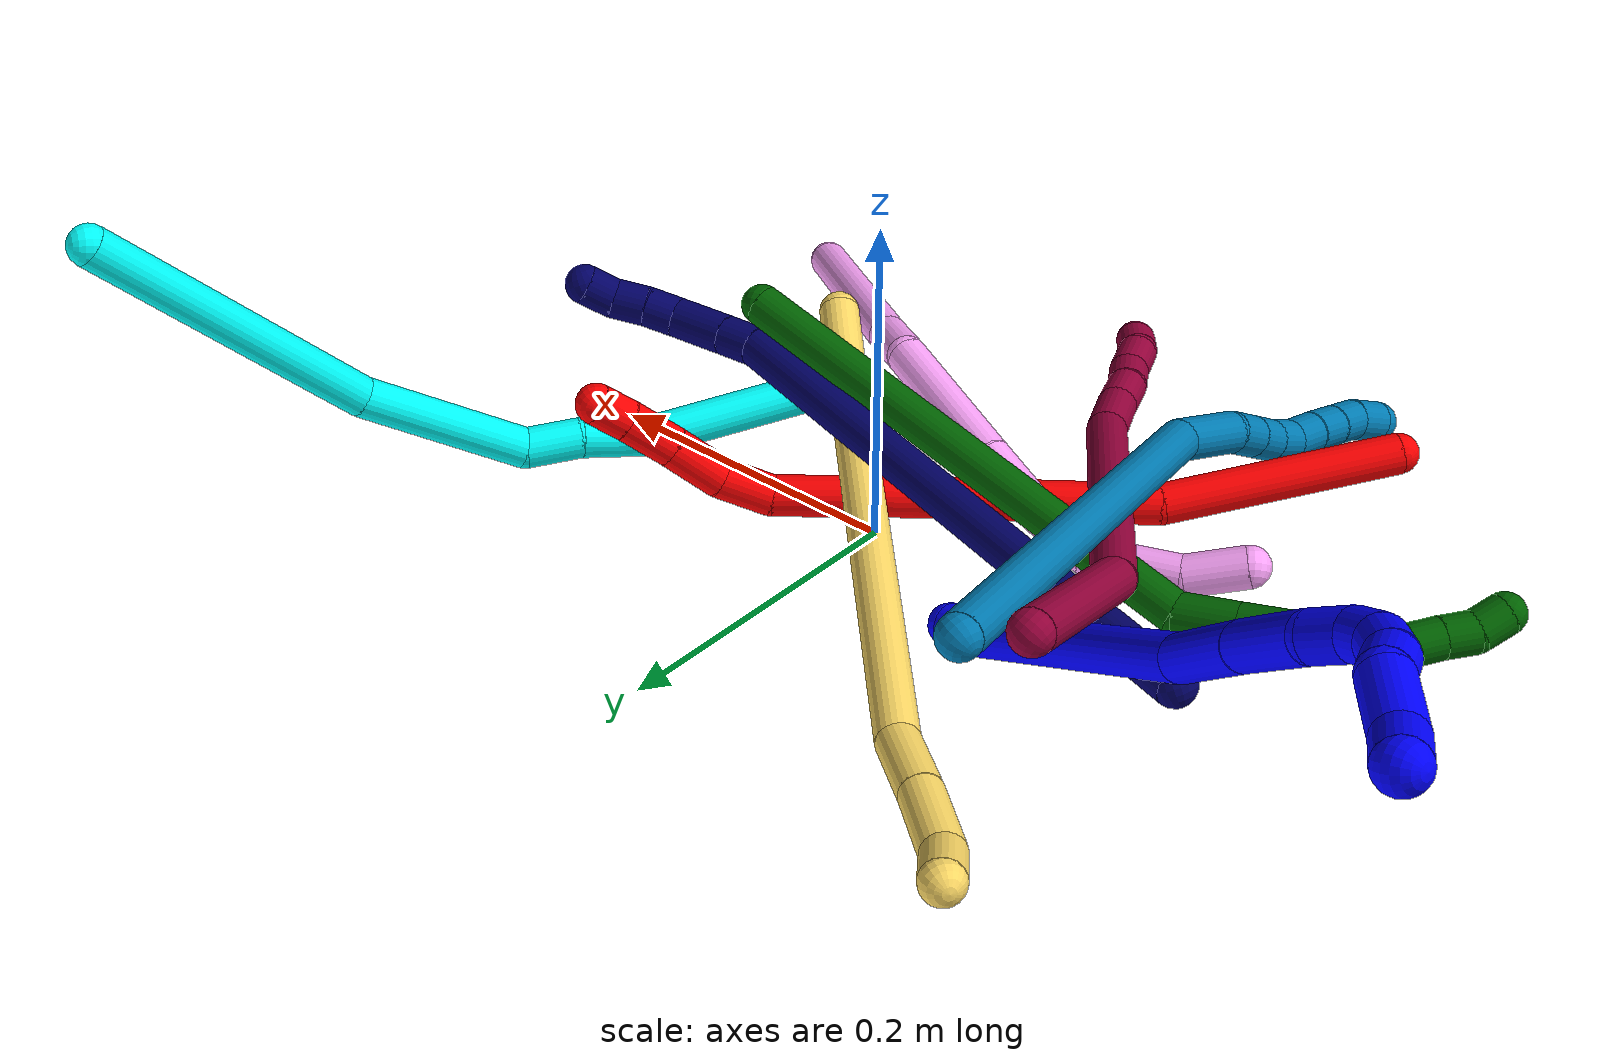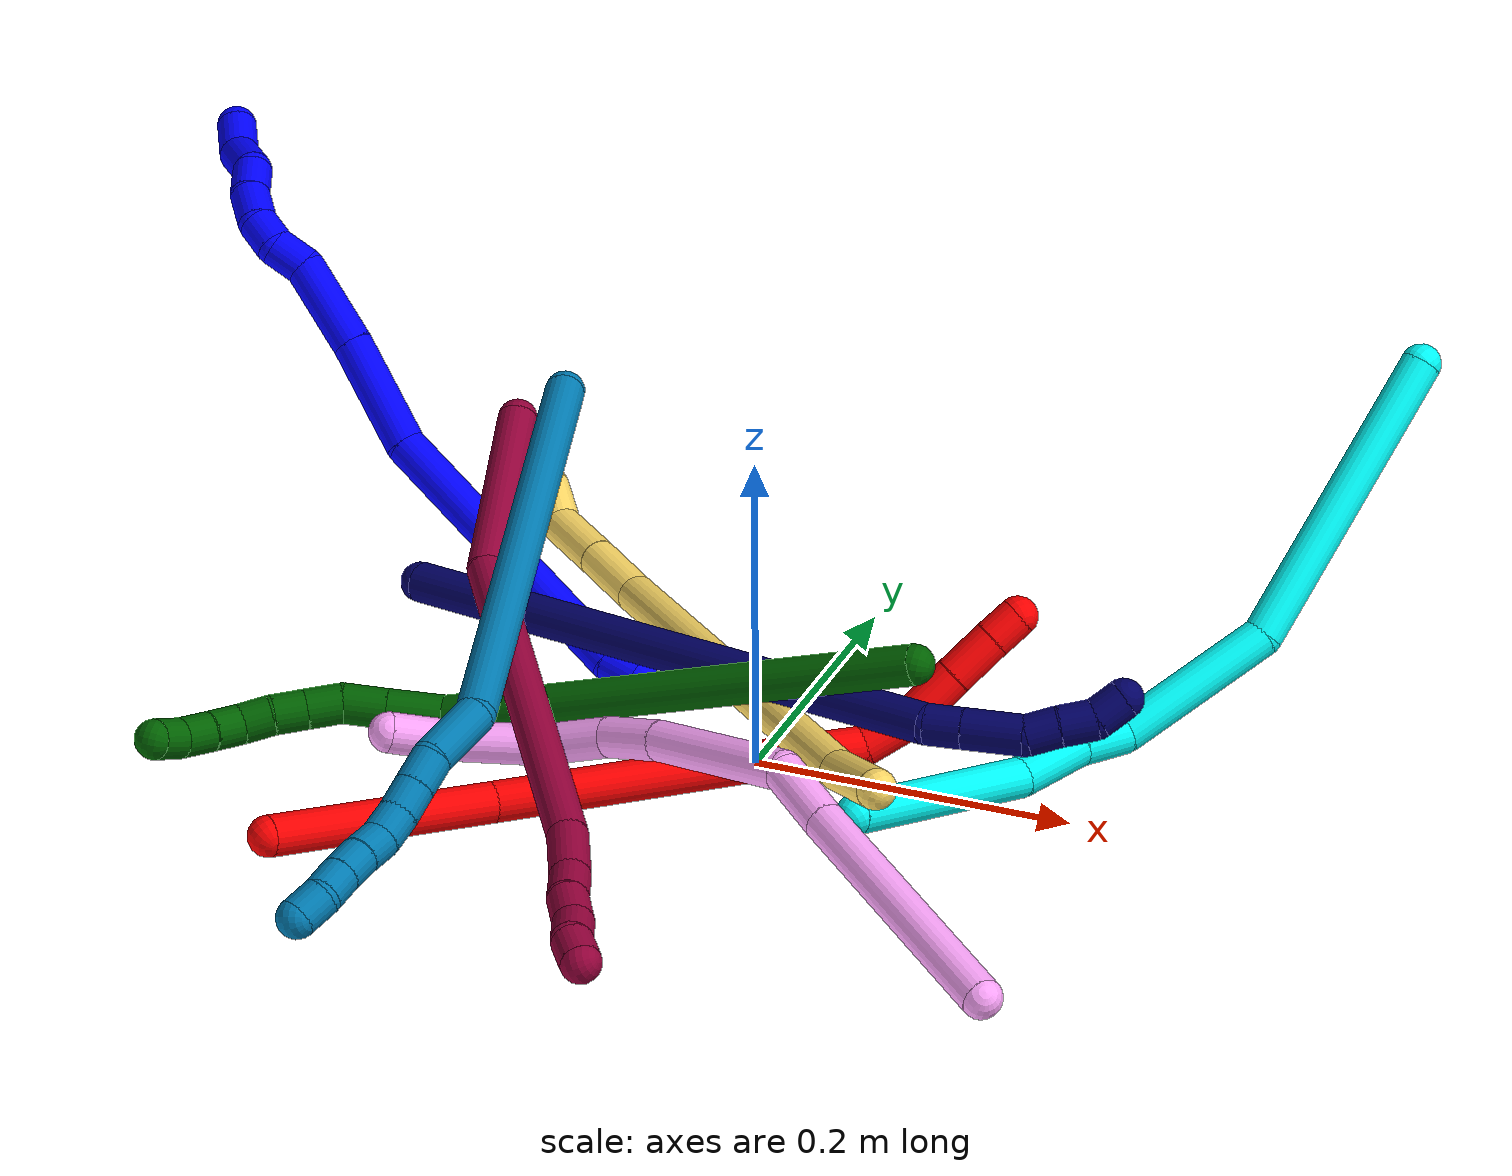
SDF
<sdf version="1.7">
 <world name="default">
  <plugin name="TubeGeneratorPlugin" filename="libtube_generator_plugin.so"/>
  <model name="photoneo_s_sensor">
   <static>1</static>
   <pose>0 0 2 1.57079 1.57079 3.14159</pose>
   <link name="link">
    <inertial><mass>0.1</mass></inertial>
    <sensor name="sensor" type="depth">
     <update_rate>30</update_rate>
     <camera>
      <horizontal_fov>1.22</horizontal_fov>
      <image><width>1920</width><height>1200</height><format>B8G8R8</format></image>
      <clip><near>0.1</near><far>4</far></clip>
      <depth_camera><output>points</output></depth_camera>
     </camera>
     <plugin name="camera_plugin" filename="libgazebo_ros_depth_camera.so">
      <baseline>0.2</baseline>
      <alwaysOn>1</alwaysOn>
      <updateRate>0.0</updateRate>
      <cameraName>camera_ir</cameraName>
      <imageTopicName>/camera/color/image_raw</imageTopicName>
      <cameraInfoTopicName>/camera/color/camera_info</cameraInfoTopicName>
      <depthImageTopicName>/camera/depth/image_raw</depthImageTopicName>
      <depthImageCameraInfoTopicName>/camera/depth/camera_info</depthImageCameraInfoTopicName>
      <pointCloudTopicName>/camera/depth/points</pointCloudTopicName>
      <frameName>fr_optical</frameName>
      <pointCloudCutoff>0.1</pointCloudCutoff>
      <pointCloudCutoffMax>2.0</pointCloudCutoffMax>
      <distortionK1>0</distortionK1>
      <distortionK2>0</distortionK2>
      <distortionK3>0</distortionK3>
      <distortionT1>0</distortionT1>
      <distortionT2>0</distortionT2>
      <CxPrime>0</CxPrime>
      <Cx>0</Cx>
      <Cy>0</Cy>
      <focalLength>0</focalLength>
      <hackBaseline>0</hackBaseline>
     </plugin>
    </sensor>
   </link>
  </model>
  <gravity>0 0 -9.8</gravity>
  <magnetic_field>6e-06 2.3e-05 -4.2e-05</magnetic_field>
  <atmosphere type="adiabatic"/>
  <physics name="default_physics" default="0" type="ode">
   <max_step_size>0.003</max_step_size>
   <real_time_factor>1</real_time_factor>
   <real_time_update_rate>1000</real_time_update_rate>
   <max_contacts>10000</max_contacts>
   <ode>
    <solver>
     <type>quick</type>
     <iters>100</iters>
     <sor>1.3</sor>
     <use_dynamic_moi_rescaling>0</use_dynamic_moi_rescaling>
    </solver>
    <constraints>
     <contact_max_correcting_vel>0</contact_max_correcting_vel>
     <contact_surface_layer>0.001</contact_surface_layer>
     <cfm>0</cfm>
     <erp>0.2</erp>
    </constraints>
   </ode>
  </physics>
  <scene><ambient>0.4 0.4 0.4 1</ambient><background>0.7 0.7 0.7 1</background><shadows>0</shadows></scene>
  <audio><device>default</device></audio>
  <spherical_coordinates>
   <surface_model>EARTH_WGS84</surface_model>
   <latitude_deg>0</latitude_deg>
   <longitude_deg>0</longitude_deg>
   <elevation>0</elevation>
   <heading_deg>0</heading_deg>
  </spherical_coordinates>
  <model name="bin">
   <static>1</static>
   <link name="bottom">
    <collision name="collision-bottom">
     <pose>0 0 -0.01 0 -0 0</pose>
     <geometry><box><size>0.8 0.6 0.02</size></box></geometry>
     <surface>
      <friction><ode><mu>100</mu><mu2>100</mu2></ode></friction>
      <contact><collide_bitmask>65535</collide_bitmask></contact>
     </surface>
    </collision>
   </link>
   <link name="west_wall">
    <collision name="collision-west_wall">
     <pose>-0.41 0 0.1 0 -0 0</pose>
     <geometry><box><size>0.02 0.6 0.2</size></box></geometry>
     <surface>
      <friction><ode><mu>100</mu><mu2>100</mu2></ode></friction>
      <contact><collide_bitmask>65535</collide_bitmask></contact>
     </surface>
    </collision>
   </link>
   <link name="east_wall">
    <collision name="collision-east_wall">
     <pose>0.41 0 0.1 0 -0 0</pose>
     <geometry><box><size>0.02 0.6 0.2</size></box></geometry>
     <surface>
      <friction><ode><mu>100</mu><mu2>100</mu2></ode></friction>
      <contact><collide_bitmask>65535</collide_bitmask></contact>
     </surface>
    </collision>
   </link>
   <link name="south_wall">
    <collision name="collision-south_wall">
     <pose>0 -0.31 0.1 0 -0 0</pose>
     <geometry><box><size>0.8 0.02 0.2</size></box></geometry>
     <surface>
      <friction><ode><mu>100</mu><mu2>100</mu2></ode></friction>
      <contact><collide_bitmask>65535</collide_bitmask></contact>
     </surface>
    </collision>
   </link>
   <link name="north_wall">
    <collision name="collision-north_wall">
     <pose>0 0.31 0.1 0 -0 0</pose>
     <geometry><box><size>0.8 0.02 0.2</size></box></geometry>
     <surface>
      <friction><ode><mu>100</mu><mu2>100</mu2></ode></friction>
      <contact><collide_bitmask>65535</collide_bitmask></contact>
     </surface>
    </collision>
   </link>
  </model>
  <model name="1">
   <static>0</static>
   <link name="1">
    <collision name="collision-cylinder-e_1_1_4">
     <pose>0.000577 -0.000716 0.011127 0.064245 0.051738 0.001663</pose>
     <geometry><cylinder><radius>0.0125</radius><length>0.02233</length></cylinder></geometry>
     <surface>
      <friction><ode><mu>1.16</mu><mu2>1.16</mu2><slip1>0</slip1><slip2>0</slip2></ode></friction>
      <contact><ode><kp>1e+06</kp><kd>1</kd><max_vel>0</max_vel><min_depth>0.001</min_depth></ode></contact>
     </surface>
    </collision>
    <visual name="visual-cylinder-e_1_1_4">
     <pose>0.000577 -0.000716 0.011127 0.064245 0.051738 0.001663</pose>
     <geometry><cylinder><radius>0.0125</radius><length>0.02233</length></cylinder></geometry>
     <material><ambient>0 0 1 1</ambient></material>
    </visual>
    <collision name="collision-cylinder-e_2_4_5">
     <pose>-0.018459 0.006513 0.115256 -0.085223 -0.207122 0.008863</pose>
     <geometry><cylinder><radius>0.0125</radius><length>0.190759</length></cylinder></geometry>
     <surface>
      <friction><ode><mu>1.16</mu><mu2>1.16</mu2><slip1>0</slip1><slip2>0</slip2></ode></friction>
      <contact><ode><kp>1e+06</kp><kd>1</kd><max_vel>0</max_vel><min_depth>0.001</min_depth></ode></contact>
     </surface>
    </collision>
    <visual name="visual-cylinder-e_2_4_5">
     <pose>-0.018459 0.006513 0.115256 -0.085223 -0.207122 0.008863</pose>
     <geometry><cylinder><radius>0.0125</radius><length>0.190759</length></cylinder></geometry>
     <material><ambient>0 0 1 1</ambient></material>
    </visual>
    <collision name="collision-cylinder-e_3_5_6">
     <pose>-0.053827 0.021449 0.240852 -0.211278 -0.441465 0.047577</pose>
     <geometry><cylinder><radius>0.0125</radius><length>0.073739</length></cylinder></geometry>
     <surface>
      <friction><ode><mu>1.16</mu><mu2>1.16</mu2><slip1>0</slip1><slip2>0</slip2></ode></friction>
      <contact><ode><kp>1e+06</kp><kd>1</kd><max_vel>0</max_vel><min_depth>0.001</min_depth></ode></contact>
     </surface>
    </collision>
    <visual name="visual-cylinder-e_3_5_6">
     <pose>-0.053827 0.021449 0.240852 -0.211278 -0.441465 0.047577</pose>
     <geometry><cylinder><radius>0.0125</radius><length>0.073739</length></cylinder></geometry>
     <material><ambient>0 0 1 1</ambient></material>
    </visual>
    <collision name="collision-cylinder-e_4_6_7">
     <pose>-0.080454 0.034024 0.300626 -0.202639 -0.373479 0.038414</pose>
     <geometry><cylinder><radius>0.0125</radius><length>0.059607</length></cylinder></geometry>
     <surface>
      <friction><ode><mu>1.16</mu><mu2>1.16</mu2><slip1>0</slip1><slip2>0</slip2></ode></friction>
      <contact><ode><kp>1e+06</kp><kd>1</kd><max_vel>0</max_vel><min_depth>0.001</min_depth></ode></contact>
     </surface>
    </collision>
    <visual name="visual-cylinder-e_4_6_7">
     <pose>-0.080454 0.034024 0.300626 -0.202639 -0.373479 0.038414</pose>
     <geometry><cylinder><radius>0.0125</radius><length>0.059607</length></cylinder></geometry>
     <material><ambient>0 0 1 1</ambient></material>
    </visual>
    <collision name="collision-cylinder-e_5_7_8">
     <pose>-0.090684 0.042115 0.338866 -0.222877 0.05673 -0.00635</pose>
     <geometry><cylinder><radius>0.0125</radius><length>0.022715</length></cylinder></geometry>
     <surface>
      <friction><ode><mu>1.16</mu><mu2>1.16</mu2><slip1>0</slip1><slip2>0</slip2></ode></friction>
      <contact><ode><kp>1e+06</kp><kd>1</kd><max_vel>0</max_vel><min_depth>0.001</min_depth></ode></contact>
     </surface>
    </collision>
    <visual name="visual-cylinder-e_5_7_8">
     <pose>-0.090684 0.042115 0.338866 -0.222877 0.05673 -0.00635</pose>
     <geometry><cylinder><radius>0.0125</radius><length>0.022715</length></cylinder></geometry>
     <material><ambient>0 0 1 1</ambient></material>
    </visual>
    <collision name="collision-cylinder-e_6_8_9">
     <pose>-0.093591 0.044467 0.359723 0.015733 -0.34768 -0.002763</pose>
     <geometry><cylinder><radius>0.0125</radius><length>0.020848</length></cylinder></geometry>
     <surface>
      <friction><ode><mu>1.16</mu><mu2>1.16</mu2><slip1>0</slip1><slip2>0</slip2></ode></friction>
      <contact><ode><kp>1e+06</kp><kd>1</kd><max_vel>0</max_vel><min_depth>0.001</min_depth></ode></contact>
     </surface>
    </collision>
    <visual name="visual-cylinder-e_6_8_9">
     <pose>-0.093591 0.044467 0.359723 0.015733 -0.34768 -0.002763</pose>
     <geometry><cylinder><radius>0.0125</radius><length>0.020848</length></cylinder></geometry>
     <material><ambient>0 0 1 1</ambient></material>
    </visual>
    <collision name="collision-cylinder-e_7_9_10">
     <pose>-0.104846 0.041794 0.378902 0.262385 -0.670566 -0.091888</pose>
     <geometry><cylinder><radius>0.0125</radius><length>0.024792</length></cylinder></geometry>
     <surface>
      <friction><ode><mu>1.16</mu><mu2>1.16</mu2><slip1>0</slip1><slip2>0</slip2></ode></friction>
      <contact><ode><kp>1e+06</kp><kd>1</kd><max_vel>0</max_vel><min_depth>0.001</min_depth></ode></contact>
     </surface>
    </collision>
    <visual name="visual-cylinder-e_7_9_10">
     <pose>-0.104846 0.041794 0.378902 0.262385 -0.670566 -0.091888</pose>
     <geometry><cylinder><radius>0.0125</radius><length>0.024792</length></cylinder></geometry>
     <material><ambient>0 0 1 1</ambient></material>
    </visual>
    <collision name="collision-cylinder-e_8_10_11">
     <pose>-0.121523 0.035994 0.394625 0.477297 -0.898623 -0.233559</pose>
     <geometry><cylinder><radius>0.0125</radius><length>0.022938</length></cylinder></geometry>
     <surface>
      <friction><ode><mu>1.16</mu><mu2>1.16</mu2><slip1>0</slip1><slip2>0</slip2></ode></friction>
      <contact><ode><kp>1e+06</kp><kd>1</kd><max_vel>0</max_vel><min_depth>0.001</min_depth></ode></contact>
     </surface>
    </collision>
    <visual name="visual-cylinder-e_8_10_11">
     <pose>-0.121523 0.035994 0.394625 0.477297 -0.898623 -0.233559</pose>
     <geometry><cylinder><radius>0.0125</radius><length>0.022938</length></cylinder></geometry>
     <material><ambient>0 0 1 1</ambient></material>
    </visual>
    <collision name="collision-cylinder-e_9_11_12">
     <pose>-0.137524 0.022112 0.412729 0.733588 -0.417661 -0.162472</pose>
     <geometry><cylinder><radius>0.0125</radius><length>0.034647</length></cylinder></geometry>
     <surface>
      <friction><ode><mu>1.16</mu><mu2>1.16</mu2><slip1>0</slip1><slip2>0</slip2></ode></friction>
      <contact><ode><kp>1e+06</kp><kd>1</kd><max_vel>0</max_vel><min_depth>0.001</min_depth></ode></contact>
     </surface>
    </collision>
    <visual name="visual-cylinder-e_9_11_12">
     <pose>-0.137524 0.022112 0.412729 0.733588 -0.417661 -0.162472</pose>
     <geometry><cylinder><radius>0.0125</radius><length>0.034647</length></cylinder></geometry>
     <material><ambient>0 0 1 1</ambient></material>
    </visual>
    <collision name="collision-cylinder-e_10_12_2">
     <pose>-0.154232 0.007482 0.433484 0.421111 -0.77653 -0.174394</pose>
     <geometry><cylinder><radius>0.0125</radius><length>0.027627</length></cylinder></geometry>
     <surface>
      <friction><ode><mu>1.16</mu><mu2>1.16</mu2><slip1>0</slip1><slip2>0</slip2></ode></friction>
      <contact><ode><kp>1e+06</kp><kd>1</kd><max_vel>0</max_vel><min_depth>0.001</min_depth></ode></contact>
     </surface>
    </collision>
    <visual name="visual-cylinder-e_10_12_2">
     <pose>-0.154232 0.007482 0.433484 0.421111 -0.77653 -0.174394</pose>
     <geometry><cylinder><radius>0.0125</radius><length>0.027627</length></cylinder></geometry>
     <material><ambient>0 0 1 1</ambient></material>
    </visual>
    <collision name="collision-sphere-2">
     <pose>-0.163912 0.003454 0.442476 0 -0 0</pose>
     <geometry><sphere><radius>0.0125</radius></sphere></geometry>
     <surface>
      <friction><ode><mu>1.16</mu><mu2>1.16</mu2><slip1>0</slip1><slip2>0</slip2></ode></friction>
      <contact><ode><kp>1e+06</kp><kd>1</kd><max_vel>0</max_vel><min_depth>0.001</min_depth></ode></contact>
     </surface>
    </collision>
    <visual name="visual-sphere-2">
     <pose>-0.163912 0.003454 0.442476 0 -0 0</pose>
     <geometry><sphere><radius>0.0125</radius></sphere></geometry>
     <material><ambient>0 0 1 1</ambient></material>
    </visual>
    <collision name="collision-sphere-12">
     <pose>-0.144551 0.01151 0.424491 0 -0 0</pose>
     <geometry><sphere><radius>0.0125</radius></sphere></geometry>
     <surface>
      <friction><ode><mu>1.16</mu><mu2>1.16</mu2><slip1>0</slip1><slip2>0</slip2></ode></friction>
      <contact><ode><kp>1e+06</kp><kd>1</kd><max_vel>0</max_vel><min_depth>0.001</min_depth></ode></contact>
     </surface>
    </collision>
    <visual name="visual-sphere-12">
     <pose>-0.144551 0.01151 0.424491 0 -0 0</pose>
     <geometry><sphere><radius>0.0125</radius></sphere></geometry>
     <material><ambient>0 0 1 1</ambient></material>
    </visual>
    <collision name="collision-sphere-11">
     <pose>-0.130497 0.032714 0.400968 0 -0 0</pose>
     <geometry><sphere><radius>0.0125</radius></sphere></geometry>
     <surface>
      <friction><ode><mu>1.16</mu><mu2>1.16</mu2><slip1>0</slip1><slip2>0</slip2></ode></friction>
      <contact><ode><kp>1e+06</kp><kd>1</kd><max_vel>0</max_vel><min_depth>0.001</min_depth></ode></contact>
     </surface>
    </collision>
    <visual name="visual-sphere-11">
     <pose>-0.130497 0.032714 0.400968 0 -0 0</pose>
     <geometry><sphere><radius>0.0125</radius></sphere></geometry>
     <material><ambient>0 0 1 1</ambient></material>
    </visual>
    <collision name="collision-sphere-10">
     <pose>-0.112549 0.039275 0.388281 0 -0 0</pose>
     <geometry><sphere><radius>0.0125</radius></sphere></geometry>
     <surface>
      <friction><ode><mu>1.16</mu><mu2>1.16</mu2><slip1>0</slip1><slip2>0</slip2></ode></friction>
      <contact><ode><kp>1e+06</kp><kd>1</kd><max_vel>0</max_vel><min_depth>0.001</min_depth></ode></contact>
     </surface>
    </collision>
    <visual name="visual-sphere-10">
     <pose>-0.112549 0.039275 0.388281 0 -0 0</pose>
     <geometry><sphere><radius>0.0125</radius></sphere></geometry>
     <material><ambient>0 0 1 1</ambient></material>
    </visual>
    <collision name="collision-sphere-9">
     <pose>-0.097143 0.044313 0.369522 0 -0 0</pose>
     <geometry><sphere><radius>0.0125</radius></sphere></geometry>
     <surface>
      <friction><ode><mu>1.16</mu><mu2>1.16</mu2><slip1>0</slip1><slip2>0</slip2></ode></friction>
      <contact><ode><kp>1e+06</kp><kd>1</kd><max_vel>0</max_vel><min_depth>0.001</min_depth></ode></contact>
     </surface>
    </collision>
    <visual name="visual-sphere-9">
     <pose>-0.097143 0.044313 0.369522 0 -0 0</pose>
     <geometry><sphere><radius>0.0125</radius></sphere></geometry>
     <material><ambient>0 0 1 1</ambient></material>
    </visual>
    <collision name="collision-sphere-4">
     <pose>0.001155 -0.001432 0.022254 0 -0 0</pose>
     <geometry><sphere><radius>0.0125</radius></sphere></geometry>
     <surface>
      <friction><ode><mu>1.16</mu><mu2>1.16</mu2><slip1>0</slip1><slip2>0</slip2></ode></friction>
      <contact><ode><kp>1e+06</kp><kd>1</kd><max_vel>0</max_vel><min_depth>0.001</min_depth></ode></contact>
     </surface>
    </collision>
    <visual name="visual-sphere-4">
     <pose>0.001155 -0.001432 0.022254 0 -0 0</pose>
     <geometry><sphere><radius>0.0125</radius></sphere></geometry>
     <material><ambient>0 0 1 1</ambient></material>
    </visual>
    <collision name="collision-sphere-1">
     <geometry><sphere><radius>0.0125</radius></sphere></geometry>
     <surface>
      <friction><ode><mu>1.16</mu><mu2>1.16</mu2><slip1>0</slip1><slip2>0</slip2></ode></friction>
      <contact><ode><kp>1e+06</kp><kd>1</kd><max_vel>0</max_vel><min_depth>0.001</min_depth></ode></contact>
     </surface>
    </collision>
    <visual name="visual-sphere-1">
     <geometry><sphere><radius>0.0125</radius></sphere></geometry>
     <material><ambient>0 0 1 1</ambient></material>
    </visual>
    <collision name="collision-sphere-8">
     <pose>-0.09004 0.044622 0.349924 0 -0 0</pose>
     <geometry><sphere><radius>0.0125</radius></sphere></geometry>
     <surface>
      <friction><ode><mu>1.16</mu><mu2>1.16</mu2><slip1>0</slip1><slip2>0</slip2></ode></friction>
      <contact><ode><kp>1e+06</kp><kd>1</kd><max_vel>0</max_vel><min_depth>0.001</min_depth></ode></contact>
     </surface>
    </collision>
    <visual name="visual-sphere-8">
     <pose>-0.09004 0.044622 0.349924 0 -0 0</pose>
     <geometry><sphere><radius>0.0125</radius></sphere></geometry>
     <material><ambient>0 0 1 1</ambient></material>
    </visual>
    <collision name="collision-sphere-5">
     <pose>-0.038074 0.014459 0.208258 0 -0 0</pose>
     <geometry><sphere><radius>0.0125</radius></sphere></geometry>
     <surface>
      <friction><ode><mu>1.16</mu><mu2>1.16</mu2><slip1>0</slip1><slip2>0</slip2></ode></friction>
      <contact><ode><kp>1e+06</kp><kd>1</kd><max_vel>0</max_vel><min_depth>0.001</min_depth></ode></contact>
     </surface>
    </collision>
    <visual name="visual-sphere-5">
     <pose>-0.038074 0.014459 0.208258 0 -0 0</pose>
     <geometry><sphere><radius>0.0125</radius></sphere></geometry>
     <material><ambient>0 0 1 1</ambient></material>
    </visual>
    <collision name="collision-sphere-6">
     <pose>-0.06958 0.02844 0.273445 0 -0 0</pose>
     <geometry><sphere><radius>0.0125</radius></sphere></geometry>
     <surface>
      <friction><ode><mu>1.16</mu><mu2>1.16</mu2><slip1>0</slip1><slip2>0</slip2></ode></friction>
      <contact><ode><kp>1e+06</kp><kd>1</kd><max_vel>0</max_vel><min_depth>0.001</min_depth></ode></contact>
     </surface>
    </collision>
    <visual name="visual-sphere-6">
     <pose>-0.06958 0.02844 0.273445 0 -0 0</pose>
     <geometry><sphere><radius>0.0125</radius></sphere></geometry>
     <material><ambient>0 0 1 1</ambient></material>
    </visual>
    <collision name="collision-sphere-7">
     <pose>-0.091328 0.039609 0.327807 0 -0 0</pose>
     <geometry><sphere><radius>0.0125</radius></sphere></geometry>
     <surface>
      <friction><ode><mu>1.16</mu><mu2>1.16</mu2><slip1>0</slip1><slip2>0</slip2></ode></friction>
      <contact><ode><kp>1e+06</kp><kd>1</kd><max_vel>0</max_vel><min_depth>0.001</min_depth></ode></contact>
     </surface>
    </collision>
    <visual name="visual-sphere-7">
     <pose>-0.091328 0.039609 0.327807 0 -0 0</pose>
     <geometry><sphere><radius>0.0125</radius></sphere></geometry>
     <material><ambient>0 0 1 1</ambient></material>
    </visual>
    <inertial>
     <pose>-0.061393 0.019109 0.235663 0 -0 0</pose>
     <mass>0.5</mass>
     <inertia>
      <ixx>0.000632</ixx>
      <ixy>0</ixy>
      <ixz>0</ixz>
      <iyy>0.000661</iyy>
      <iyz>0</iyz>
      <izz>0.00013</izz>
     </inertia>
    </inertial>
   </link>
   <pose>-0.099406 0.054924 0.011475 1.18275 0.469855 -1.91726</pose>
  </model>
  <model name="2">
   <static>0</static>
   <link name="2">
    <collision name="collision-cylinder-e_1_1_4">
     <pose>0.062499 0.038653 0.00422 -1.46206 1.01426 -0.924487</pose>
     <geometry><cylinder><radius>0.0125</radius><length>0.147213</length></cylinder></geometry>
     <surface>
      <friction><ode><mu>1.16</mu><mu2>1.16</mu2><slip1>0</slip1><slip2>0</slip2></ode></friction>
      <contact><ode><kp>1e+06</kp><kd>1</kd><max_vel>0</max_vel><min_depth>0.001</min_depth></ode></contact>
     </surface>
    </collision>
    <visual name="visual-cylinder-e_1_1_4">
     <pose>0.062499 0.038653 0.00422 -1.46206 1.01426 -0.924487</pose>
     <geometry><cylinder><radius>0.0125</radius><length>0.147213</length></cylinder></geometry>
     <material><ambient>1 0 0 1</ambient></material>
    </visual>
    <collision name="collision-cylinder-e_2_4_5">
     <pose>0.185205 0.132095 0.028837 -1.21442 0.800097 -0.571488</pose>
     <geometry><cylinder><radius>0.0125</radius><length>0.167845</length></cylinder></geometry>
     <surface>
      <friction><ode><mu>1.16</mu><mu2>1.16</mu2><slip1>0</slip1><slip2>0</slip2></ode></friction>
      <contact><ode><kp>1e+06</kp><kd>1</kd><max_vel>0</max_vel><min_depth>0.001</min_depth></ode></contact>
     </surface>
    </collision>
    <visual name="visual-cylinder-e_2_4_5">
     <pose>0.185205 0.132095 0.028837 -1.21442 0.800097 -0.571488</pose>
     <geometry><cylinder><radius>0.0125</radius><length>0.167845</length></cylinder></geometry>
     <material><ambient>1 0 0 1</ambient></material>
    </visual>
    <collision name="collision-cylinder-e_3_5_6">
     <pose>0.268393 0.206695 0.056746 -1.20832 0.825975 -0.587433</pose>
     <geometry><cylinder><radius>0.0125</radius><length>0.062513</length></cylinder></geometry>
     <surface>
      <friction><ode><mu>1.16</mu><mu2>1.16</mu2><slip1>0</slip1><slip2>0</slip2></ode></friction>
      <contact><ode><kp>1e+06</kp><kd>1</kd><max_vel>0</max_vel><min_depth>0.001</min_depth></ode></contact>
     </surface>
    </collision>
    <visual name="visual-cylinder-e_3_5_6">
     <pose>0.268393 0.206695 0.056746 -1.20832 0.825975 -0.587433</pose>
     <geometry><cylinder><radius>0.0125</radius><length>0.062513</length></cylinder></geometry>
     <material><ambient>1 0 0 1</ambient></material>
    </visual>
    <collision name="collision-cylinder-e_4_6_7">
     <pose>0.298659 0.241469 0.065617 -1.48028 0.451491 -0.413524</pose>
     <geometry><cylinder><radius>0.0125</radius><length>0.033396</length></cylinder></geometry>
     <surface>
      <friction><ode><mu>1.16</mu><mu2>1.16</mu2><slip1>0</slip1><slip2>0</slip2></ode></friction>
      <contact><ode><kp>1e+06</kp><kd>1</kd><max_vel>0</max_vel><min_depth>0.001</min_depth></ode></contact>
     </surface>
    </collision>
    <visual name="visual-cylinder-e_4_6_7">
     <pose>0.298659 0.241469 0.065617 -1.48028 0.451491 -0.413524</pose>
     <geometry><cylinder><radius>0.0125</radius><length>0.033396</length></cylinder></geometry>
     <material><ambient>1 0 0 1</ambient></material>
    </visual>
    <collision name="collision-cylinder-e_5_7_8">
     <pose>0.309537 0.274146 0.066312 -1.6082 0.199964 -0.207534</pose>
     <geometry><cylinder><radius>0.0125</radius><length>0.036172</length></cylinder></geometry>
     <surface>
      <friction><ode><mu>1.16</mu><mu2>1.16</mu2><slip1>0</slip1><slip2>0</slip2></ode></friction>
      <contact><ode><kp>1e+06</kp><kd>1</kd><max_vel>0</max_vel><min_depth>0.001</min_depth></ode></contact>
     </surface>
    </collision>
    <visual name="visual-cylinder-e_5_7_8">
     <pose>0.309537 0.274146 0.066312 -1.6082 0.199964 -0.207534</pose>
     <geometry><cylinder><radius>0.0125</radius><length>0.036172</length></cylinder></geometry>
     <material><ambient>1 0 0 1</ambient></material>
    </visual>
    <collision name="collision-cylinder-e_6_8_9">
     <pose>0.31691 0.307333 0.064945 -1.61629 0.239376 -0.250409</pose>
     <geometry><cylinder><radius>0.0125</radius><length>0.03189</length></cylinder></geometry>
     <surface>
      <friction><ode><mu>1.16</mu><mu2>1.16</mu2><slip1>0</slip1><slip2>0</slip2></ode></friction>
      <contact><ode><kp>1e+06</kp><kd>1</kd><max_vel>0</max_vel><min_depth>0.001</min_depth></ode></contact>
     </surface>
    </collision>
    <visual name="visual-cylinder-e_6_8_9">
     <pose>0.31691 0.307333 0.064945 -1.61629 0.239376 -0.250409</pose>
     <geometry><cylinder><radius>0.0125</radius><length>0.03189</length></cylinder></geometry>
     <material><ambient>1 0 0 1</ambient></material>
    </visual>
    <collision name="collision-cylinder-e_7_9_2">
     <pose>0.323683 0.332847 0.063791 -1.6155 0.289435 -0.302476</pose>
     <geometry><cylinder><radius>0.0125</radius><length>0.020971</length></cylinder></geometry>
     <surface>
      <friction><ode><mu>1.16</mu><mu2>1.16</mu2><slip1>0</slip1><slip2>0</slip2></ode></friction>
      <contact><ode><kp>1e+06</kp><kd>1</kd><max_vel>0</max_vel><min_depth>0.001</min_depth></ode></contact>
     </surface>
    </collision>
    <visual name="visual-cylinder-e_7_9_2">
     <pose>0.323683 0.332847 0.063791 -1.6155 0.289435 -0.302476</pose>
     <geometry><cylinder><radius>0.0125</radius><length>0.020971</length></cylinder></geometry>
     <material><ambient>1 0 0 1</ambient></material>
    </visual>
    <collision name="collision-sphere-2">
     <pose>0.326676 0.342886 0.063342 0 -0 0</pose>
     <geometry><sphere><radius>0.0125</radius></sphere></geometry>
     <surface>
      <friction><ode><mu>1.16</mu><mu2>1.16</mu2><slip1>0</slip1><slip2>0</slip2></ode></friction>
      <contact><ode><kp>1e+06</kp><kd>1</kd><max_vel>0</max_vel><min_depth>0.001</min_depth></ode></contact>
     </surface>
    </collision>
    <visual name="visual-sphere-2">
     <pose>0.326676 0.342886 0.063342 0 -0 0</pose>
     <geometry><sphere><radius>0.0125</radius></sphere></geometry>
     <material><ambient>1 0 0 1</ambient></material>
    </visual>
    <collision name="collision-sphere-9">
     <pose>0.320691 0.322807 0.06424 0 -0 0</pose>
     <geometry><sphere><radius>0.0125</radius></sphere></geometry>
     <surface>
      <friction><ode><mu>1.16</mu><mu2>1.16</mu2><slip1>0</slip1><slip2>0</slip2></ode></friction>
      <contact><ode><kp>1e+06</kp><kd>1</kd><max_vel>0</max_vel><min_depth>0.001</min_depth></ode></contact>
     </surface>
    </collision>
    <visual name="visual-sphere-9">
     <pose>0.320691 0.322807 0.06424 0 -0 0</pose>
     <geometry><sphere><radius>0.0125</radius></sphere></geometry>
     <material><ambient>1 0 0 1</ambient></material>
    </visual>
    <collision name="collision-sphere-4">
     <pose>0.124997 0.077305 0.008439 0 -0 0</pose>
     <geometry><sphere><radius>0.0125</radius></sphere></geometry>
     <surface>
      <friction><ode><mu>1.16</mu><mu2>1.16</mu2><slip1>0</slip1><slip2>0</slip2></ode></friction>
      <contact><ode><kp>1e+06</kp><kd>1</kd><max_vel>0</max_vel><min_depth>0.001</min_depth></ode></contact>
     </surface>
    </collision>
    <visual name="visual-sphere-4">
     <pose>0.124997 0.077305 0.008439 0 -0 0</pose>
     <geometry><sphere><radius>0.0125</radius></sphere></geometry>
     <material><ambient>1 0 0 1</ambient></material>
    </visual>
    <collision name="collision-sphere-1">
     <geometry><sphere><radius>0.0125</radius></sphere></geometry>
     <surface>
      <friction><ode><mu>1.16</mu><mu2>1.16</mu2><slip1>0</slip1><slip2>0</slip2></ode></friction>
      <contact><ode><kp>1e+06</kp><kd>1</kd><max_vel>0</max_vel><min_depth>0.001</min_depth></ode></contact>
     </surface>
    </collision>
    <visual name="visual-sphere-1">
     <geometry><sphere><radius>0.0125</radius></sphere></geometry>
     <material><ambient>1 0 0 1</ambient></material>
    </visual>
    <collision name="collision-sphere-8">
     <pose>0.31313 0.291859 0.065649 0 -0 0</pose>
     <geometry><sphere><radius>0.0125</radius></sphere></geometry>
     <surface>
      <friction><ode><mu>1.16</mu><mu2>1.16</mu2><slip1>0</slip1><slip2>0</slip2></ode></friction>
      <contact><ode><kp>1e+06</kp><kd>1</kd><max_vel>0</max_vel><min_depth>0.001</min_depth></ode></contact>
     </surface>
    </collision>
    <visual name="visual-sphere-8">
     <pose>0.31313 0.291859 0.065649 0 -0 0</pose>
     <geometry><sphere><radius>0.0125</radius></sphere></geometry>
     <material><ambient>1 0 0 1</ambient></material>
    </visual>
    <collision name="collision-sphere-5">
     <pose>0.245413 0.186885 0.049234 0 -0 0</pose>
     <geometry><sphere><radius>0.0125</radius></sphere></geometry>
     <surface>
      <friction><ode><mu>1.16</mu><mu2>1.16</mu2><slip1>0</slip1><slip2>0</slip2></ode></friction>
      <contact><ode><kp>1e+06</kp><kd>1</kd><max_vel>0</max_vel><min_depth>0.001</min_depth></ode></contact>
     </surface>
    </collision>
    <visual name="visual-sphere-5">
     <pose>0.245413 0.186885 0.049234 0 -0 0</pose>
     <geometry><sphere><radius>0.0125</radius></sphere></geometry>
     <material><ambient>1 0 0 1</ambient></material>
    </visual>
    <collision name="collision-sphere-6">
     <pose>0.291373 0.226506 0.064259 0 -0 0</pose>
     <geometry><sphere><radius>0.0125</radius></sphere></geometry>
     <surface>
      <friction><ode><mu>1.16</mu><mu2>1.16</mu2><slip1>0</slip1><slip2>0</slip2></ode></friction>
      <contact><ode><kp>1e+06</kp><kd>1</kd><max_vel>0</max_vel><min_depth>0.001</min_depth></ode></contact>
     </surface>
    </collision>
    <visual name="visual-sphere-6">
     <pose>0.291373 0.226506 0.064259 0 -0 0</pose>
     <geometry><sphere><radius>0.0125</radius></sphere></geometry>
     <material><ambient>1 0 0 1</ambient></material>
    </visual>
    <collision name="collision-sphere-7">
     <pose>0.305945 0.256433 0.066975 0 -0 0</pose>
     <geometry><sphere><radius>0.0125</radius></sphere></geometry>
     <surface>
      <friction><ode><mu>1.16</mu><mu2>1.16</mu2><slip1>0</slip1><slip2>0</slip2></ode></friction>
      <contact><ode><kp>1e+06</kp><kd>1</kd><max_vel>0</max_vel><min_depth>0.001</min_depth></ode></contact>
     </surface>
    </collision>
    <visual name="visual-sphere-7">
     <pose>0.305945 0.256433 0.066975 0 -0 0</pose>
     <geometry><sphere><radius>0.0125</radius></sphere></geometry>
     <material><ambient>1 0 0 1</ambient></material>
    </visual>
    <inertial>
     <pose>0.190259 0.151089 0.034015 0 -0 0</pose>
     <mass>0.5</mass>
     <inertia>
      <ixx>9.5e-05</ixx>
      <ixy>0</ixy>
      <ixz>0</ixz>
      <iyy>0.000229</iyy>
      <iyz>0</iyz>
      <izz>-0.000967</izz>
     </inertia>
    </inertial>
   </link>
   <pose>-0.210618 -0.235106 0.030195 1.86732 0.649611 1.11023</pose>
  </model>
  <model name="3">
   <static>0</static>
   <link name="3">
    <collision name="collision-cylinder-e_1_1_4">
     <pose>-0.011588 0.050584 -0.082127 -2.58955 -0.119561 0.416477</pose>
     <geometry><cylinder><radius>0.0125</radius><length>0.194297</length></cylinder></geometry>
     <surface>
      <friction><ode><mu>1.16</mu><mu2>1.16</mu2><slip1>0</slip1><slip2>0</slip2></ode></friction>
      <contact><ode><kp>1e+06</kp><kd>1</kd><max_vel>0</max_vel><min_depth>0.001</min_depth></ode></contact>
     </surface>
    </collision>
    <visual name="visual-cylinder-e_1_1_4">
     <pose>-0.011588 0.050584 -0.082127 -2.58955 -0.119561 0.416477</pose>
     <geometry><cylinder><radius>0.0125</radius><length>0.194297</length></cylinder></geometry>
     <material><ambient>0.003922 1 0.996078 1</ambient></material>
    </visual>
    <collision name="collision-cylinder-e_2_4_5">
     <pose>-0.040952 0.110059 -0.212188 -2.95818 -0.349654 2.18152</pose>
     <geometry><cylinder><radius>0.0125</radius><length>0.103783</length></cylinder></geometry>
     <surface>
      <friction><ode><mu>1.16</mu><mu2>1.16</mu2><slip1>0</slip1><slip2>0</slip2></ode></friction>
      <contact><ode><kp>1e+06</kp><kd>1</kd><max_vel>0</max_vel><min_depth>0.001</min_depth></ode></contact>
     </surface>
    </collision>
    <visual name="visual-cylinder-e_2_4_5">
     <pose>-0.040952 0.110059 -0.212188 -2.95818 -0.349654 2.18152</pose>
     <geometry><cylinder><radius>0.0125</radius><length>0.103783</length></cylinder></geometry>
     <material><ambient>0.003922 1 0.996078 1</ambient></material>
    </visual>
    <collision name="collision-cylinder-e_3_5_6">
     <pose>-0.061003 0.114065 -0.276443 2.85073 -0.132718 -0.851926</pose>
     <geometry><cylinder><radius>0.0125</radius><length>0.034377</length></cylinder></geometry>
     <surface>
      <friction><ode><mu>1.16</mu><mu2>1.16</mu2><slip1>0</slip1><slip2>0</slip2></ode></friction>
      <contact><ode><kp>1e+06</kp><kd>1</kd><max_vel>0</max_vel><min_depth>0.001</min_depth></ode></contact>
     </surface>
    </collision>
    <visual name="visual-cylinder-e_3_5_6">
     <pose>-0.061003 0.114065 -0.276443 2.85073 -0.132718 -0.851926</pose>
     <geometry><cylinder><radius>0.0125</radius><length>0.034377</length></cylinder></geometry>
     <material><ambient>0.003922 1 0.996078 1</ambient></material>
    </visual>
    <collision name="collision-cylinder-e_4_6_7">
     <pose>-0.06643 0.107449 -0.314794 3.06321 -0.141712 -2.13214</pose>
     <geometry><cylinder><radius>0.0125</radius><length>0.044642</length></cylinder></geometry>
     <surface>
      <friction><ode><mu>1.16</mu><mu2>1.16</mu2><slip1>0</slip1><slip2>0</slip2></ode></friction>
      <contact><ode><kp>1e+06</kp><kd>1</kd><max_vel>0</max_vel><min_depth>0.001</min_depth></ode></contact>
     </surface>
    </collision>
    <visual name="visual-cylinder-e_4_6_7">
     <pose>-0.06643 0.107449 -0.314794 3.06321 -0.141712 -2.13214</pose>
     <geometry><cylinder><radius>0.0125</radius><length>0.044642</length></cylinder></geometry>
     <material><ambient>0.003922 1 0.996078 1</ambient></material>
    </visual>
    <collision name="collision-cylinder-e_5_7_2">
     <pose>-0.074453 0.084272 -0.394204 2.7839 -0.079343 -0.432273</pose>
     <geometry><cylinder><radius>0.0125</radius><length>0.122901</length></cylinder></geometry>
     <surface>
      <friction><ode><mu>1.16</mu><mu2>1.16</mu2><slip1>0</slip1><slip2>0</slip2></ode></friction>
      <contact><ode><kp>1e+06</kp><kd>1</kd><max_vel>0</max_vel><min_depth>0.001</min_depth></ode></contact>
     </surface>
    </collision>
    <visual name="visual-cylinder-e_5_7_2">
     <pose>-0.074453 0.084272 -0.394204 2.7839 -0.079343 -0.432273</pose>
     <geometry><cylinder><radius>0.0125</radius><length>0.122901</length></cylinder></geometry>
     <material><ambient>0.003922 1 0.996078 1</ambient></material>
    </visual>
    <collision name="collision-sphere-2">
     <pose>-0.079324 0.062825 -0.451584 0 -0 0</pose>
     <geometry><sphere><radius>0.0125</radius></sphere></geometry>
     <surface>
      <friction><ode><mu>1.16</mu><mu2>1.16</mu2><slip1>0</slip1><slip2>0</slip2></ode></friction>
      <contact><ode><kp>1e+06</kp><kd>1</kd><max_vel>0</max_vel><min_depth>0.001</min_depth></ode></contact>
     </surface>
    </collision>
    <visual name="visual-sphere-2">
     <pose>-0.079324 0.062825 -0.451584 0 -0 0</pose>
     <geometry><sphere><radius>0.0125</radius></sphere></geometry>
     <material><ambient>0.003922 1 0.996078 1</ambient></material>
    </visual>
    <collision name="collision-sphere-7">
     <pose>-0.069583 0.105719 -0.336824 0 -0 0</pose>
     <geometry><sphere><radius>0.0125</radius></sphere></geometry>
     <surface>
      <friction><ode><mu>1.16</mu><mu2>1.16</mu2><slip1>0</slip1><slip2>0</slip2></ode></friction>
      <contact><ode><kp>1e+06</kp><kd>1</kd><max_vel>0</max_vel><min_depth>0.001</min_depth></ode></contact>
     </surface>
    </collision>
    <visual name="visual-sphere-7">
     <pose>-0.069583 0.105719 -0.336824 0 -0 0</pose>
     <geometry><sphere><radius>0.0125</radius></sphere></geometry>
     <material><ambient>0.003922 1 0.996078 1</ambient></material>
    </visual>
    <collision name="collision-sphere-6">
     <pose>-0.063277 0.109179 -0.292765 0 -0 0</pose>
     <geometry><sphere><radius>0.0125</radius></sphere></geometry>
     <surface>
      <friction><ode><mu>1.16</mu><mu2>1.16</mu2><slip1>0</slip1><slip2>0</slip2></ode></friction>
      <contact><ode><kp>1e+06</kp><kd>1</kd><max_vel>0</max_vel><min_depth>0.001</min_depth></ode></contact>
     </surface>
    </collision>
    <visual name="visual-sphere-6">
     <pose>-0.063277 0.109179 -0.292765 0 -0 0</pose>
     <geometry><sphere><radius>0.0125</radius></sphere></geometry>
     <material><ambient>0.003922 1 0.996078 1</ambient></material>
    </visual>
    <collision name="collision-sphere-5">
     <pose>-0.058728 0.118951 -0.260122 0 -0 0</pose>
     <geometry><sphere><radius>0.0125</radius></sphere></geometry>
     <surface>
      <friction><ode><mu>1.16</mu><mu2>1.16</mu2><slip1>0</slip1><slip2>0</slip2></ode></friction>
      <contact><ode><kp>1e+06</kp><kd>1</kd><max_vel>0</max_vel><min_depth>0.001</min_depth></ode></contact>
     </surface>
    </collision>
    <visual name="visual-sphere-5">
     <pose>-0.058728 0.118951 -0.260122 0 -0 0</pose>
     <geometry><sphere><radius>0.0125</radius></sphere></geometry>
     <material><ambient>0.003922 1 0.996078 1</ambient></material>
    </visual>
    <collision name="collision-sphere-1">
     <geometry><sphere><radius>0.0125</radius></sphere></geometry>
     <surface>
      <friction><ode><mu>1.16</mu><mu2>1.16</mu2><slip1>0</slip1><slip2>0</slip2></ode></friction>
      <contact><ode><kp>1e+06</kp><kd>1</kd><max_vel>0</max_vel><min_depth>0.001</min_depth></ode></contact>
     </surface>
    </collision>
    <visual name="visual-sphere-1">
     <geometry><sphere><radius>0.0125</radius></sphere></geometry>
     <material><ambient>0.003922 1 0.996078 1</ambient></material>
    </visual>
    <collision name="collision-sphere-4">
     <pose>-0.023175 0.101168 -0.164254 0 -0 0</pose>
     <geometry><sphere><radius>0.0125</radius></sphere></geometry>
     <surface>
      <friction><ode><mu>1.16</mu><mu2>1.16</mu2><slip1>0</slip1><slip2>0</slip2></ode></friction>
      <contact><ode><kp>1e+06</kp><kd>1</kd><max_vel>0</max_vel><min_depth>0.001</min_depth></ode></contact>
     </surface>
    </collision>
    <visual name="visual-sphere-4">
     <pose>-0.023175 0.101168 -0.164254 0 -0 0</pose>
     <geometry><sphere><radius>0.0125</radius></sphere></geometry>
     <material><ambient>0.003922 1 0.996078 1</ambient></material>
    </visual>
    <inertial>
     <pose>-0.041429 0.080651 -0.219966 0 -0 0</pose>
     <mass>0.5</mass>
     <inertia>
      <ixx>0.000892</ixx>
      <ixy>0</ixy>
      <ixz>0</ixz>
      <iyy>-0.000288</iyy>
      <iyz>0</iyz>
      <izz>-0.000195</izz>
     </inertia>
    </inertial>
   </link>
   <pose>0.320967 0.287701 0.193841 -1.36854 -0.222199 -0.445579</pose>
  </model>
  <model name="4">
   <static>0</static>
   <link name="4">
    <collision name="collision-cylinder-e_1_1_4">
     <pose>-0.053082 0.048563 -0.044909 -2.31713 -0.676273 1.35452</pose>
     <geometry><cylinder><radius>0.0125</radius><length>0.169622</length></cylinder></geometry>
     <surface>
      <friction><ode><mu>1.16</mu><mu2>1.16</mu2><slip1>0</slip1><slip2>0</slip2></ode></friction>
      <contact><ode><kp>1e+06</kp><kd>1</kd><max_vel>0</max_vel><min_depth>0.001</min_depth></ode></contact>
     </surface>
    </collision>
    <visual name="visual-cylinder-e_1_1_4">
     <pose>-0.053082 0.048563 -0.044909 -2.31713 -0.676273 1.35452</pose>
     <geometry><cylinder><radius>0.0125</radius><length>0.169622</length></cylinder></geometry>
     <material><ambient>1 0.65098 0.996078 1</ambient></material>
    </visual>
    <collision name="collision-cylinder-e_2_4_5">
     <pose>-0.121157 0.111408 -0.10151 -2.25679 -0.682162 1.2861</pose>
     <geometry><cylinder><radius>0.0125</radius><length>0.047559</length></cylinder></geometry>
     <surface>
      <friction><ode><mu>1.16</mu><mu2>1.16</mu2><slip1>0</slip1><slip2>0</slip2></ode></friction>
      <contact><ode><kp>1e+06</kp><kd>1</kd><max_vel>0</max_vel><min_depth>0.001</min_depth></ode></contact>
     </surface>
    </collision>
    <visual name="visual-cylinder-e_2_4_5">
     <pose>-0.121157 0.111408 -0.10151 -2.25679 -0.682162 1.2861</pose>
     <geometry><cylinder><radius>0.0125</radius><length>0.047559</length></cylinder></geometry>
     <material><ambient>1 0.65098 0.996078 1</ambient></material>
    </visual>
    <collision name="collision-cylinder-e_3_5_6">
     <pose>-0.170414 0.133719 -0.149453 -2.92366 -0.745291 2.59582</pose>
     <geometry><cylinder><radius>0.0125</radius><length>0.101047</length></cylinder></geometry>
     <surface>
      <friction><ode><mu>1.16</mu><mu2>1.16</mu2><slip1>0</slip1><slip2>0</slip2></ode></friction>
      <contact><ode><kp>1e+06</kp><kd>1</kd><max_vel>0</max_vel><min_depth>0.001</min_depth></ode></contact>
     </surface>
    </collision>
    <visual name="visual-cylinder-e_3_5_6">
     <pose>-0.170414 0.133719 -0.149453 -2.92366 -0.745291 2.59582</pose>
     <geometry><cylinder><radius>0.0125</radius><length>0.101047</length></cylinder></geometry>
     <material><ambient>1 0.65098 0.996078 1</ambient></material>
    </visual>
    <collision name="collision-cylinder-e_4_6_7">
     <pose>-0.21839 0.142554 -0.200757 -3.08805 -0.738073 3.00335</pose>
     <geometry><cylinder><radius>0.0125</radius><length>0.040756</length></cylinder></geometry>
     <surface>
      <friction><ode><mu>1.16</mu><mu2>1.16</mu2><slip1>0</slip1><slip2>0</slip2></ode></friction>
      <contact><ode><kp>1e+06</kp><kd>1</kd><max_vel>0</max_vel><min_depth>0.001</min_depth></ode></contact>
     </surface>
    </collision>
    <visual name="visual-cylinder-e_4_6_7">
     <pose>-0.21839 0.142554 -0.200757 -3.08805 -0.738073 3.00335</pose>
     <geometry><cylinder><radius>0.0125</radius><length>0.040756</length></cylinder></geometry>
     <material><ambient>1 0.65098 0.996078 1</ambient></material>
    </visual>
    <collision name="collision-cylinder-e_5_7_8">
     <pose>-0.250079 0.138931 -0.231862 2.87234 -0.823674 -2.54025</pose>
     <geometry><cylinder><radius>0.0125</radius><length>0.049009</length></cylinder></geometry>
     <surface>
      <friction><ode><mu>1.16</mu><mu2>1.16</mu2><slip1>0</slip1><slip2>0</slip2></ode></friction>
      <contact><ode><kp>1e+06</kp><kd>1</kd><max_vel>0</max_vel><min_depth>0.001</min_depth></ode></contact>
     </surface>
    </collision>
    <visual name="visual-cylinder-e_5_7_8">
     <pose>-0.250079 0.138931 -0.231862 2.87234 -0.823674 -2.54025</pose>
     <geometry><cylinder><radius>0.0125</radius><length>0.049009</length></cylinder></geometry>
     <material><ambient>1 0.65098 0.996078 1</ambient></material>
    </visual>
    <collision name="collision-cylinder-e_6_8_9">
     <pose>-0.293914 0.128036 -0.253464 2.28017 -1.25249 -2.00981</pose>
     <geometry><cylinder><radius>0.0125</radius><length>0.054451</length></cylinder></geometry>
     <surface>
      <friction><ode><mu>1.16</mu><mu2>1.16</mu2><slip1>0</slip1><slip2>0</slip2></ode></friction>
      <contact><ode><kp>1e+06</kp><kd>1</kd><max_vel>0</max_vel><min_depth>0.001</min_depth></ode></contact>
     </surface>
    </collision>
    <visual name="visual-cylinder-e_6_8_9">
     <pose>-0.293914 0.128036 -0.253464 2.28017 -1.25249 -2.00981</pose>
     <geometry><cylinder><radius>0.0125</radius><length>0.054451</length></cylinder></geometry>
     <material><ambient>1 0.65098 0.996078 1</ambient></material>
    </visual>
    <collision name="collision-cylinder-e_7_9_2">
     <pose>-0.337675 0.116571 -0.256349 1.08122 -1.26428 -0.828395</pose>
     <geometry><cylinder><radius>0.0125</radius><length>0.037556</length></cylinder></geometry>
     <surface>
      <friction><ode><mu>1.16</mu><mu2>1.16</mu2><slip1>0</slip1><slip2>0</slip2></ode></friction>
      <contact><ode><kp>1e+06</kp><kd>1</kd><max_vel>0</max_vel><min_depth>0.001</min_depth></ode></contact>
     </surface>
    </collision>
    <visual name="visual-cylinder-e_7_9_2">
     <pose>-0.337675 0.116571 -0.256349 1.08122 -1.26428 -0.828395</pose>
     <geometry><cylinder><radius>0.0125</radius><length>0.037556</length></cylinder></geometry>
     <material><ambient>1 0.65098 0.996078 1</ambient></material>
    </visual>
    <collision name="collision-sphere-2">
     <pose>-0.355578 0.11157 -0.253685 0 -0 0</pose>
     <geometry><sphere><radius>0.0125</radius></sphere></geometry>
     <surface>
      <friction><ode><mu>1.16</mu><mu2>1.16</mu2><slip1>0</slip1><slip2>0</slip2></ode></friction>
      <contact><ode><kp>1e+06</kp><kd>1</kd><max_vel>0</max_vel><min_depth>0.001</min_depth></ode></contact>
     </surface>
    </collision>
    <visual name="visual-sphere-2">
     <pose>-0.355578 0.11157 -0.253685 0 -0 0</pose>
     <geometry><sphere><radius>0.0125</radius></sphere></geometry>
     <material><ambient>1 0.65098 0.996078 1</ambient></material>
    </visual>
    <collision name="collision-sphere-9">
     <pose>-0.319772 0.121571 -0.259014 0 -0 0</pose>
     <geometry><sphere><radius>0.0125</radius></sphere></geometry>
     <surface>
      <friction><ode><mu>1.16</mu><mu2>1.16</mu2><slip1>0</slip1><slip2>0</slip2></ode></friction>
      <contact><ode><kp>1e+06</kp><kd>1</kd><max_vel>0</max_vel><min_depth>0.001</min_depth></ode></contact>
     </surface>
    </collision>
    <visual name="visual-sphere-9">
     <pose>-0.319772 0.121571 -0.259014 0 -0 0</pose>
     <geometry><sphere><radius>0.0125</radius></sphere></geometry>
     <material><ambient>1 0.65098 0.996078 1</ambient></material>
    </visual>
    <collision name="collision-sphere-4">
     <pose>-0.106165 0.097126 -0.089818 0 -0 0</pose>
     <geometry><sphere><radius>0.0125</radius></sphere></geometry>
     <surface>
      <friction><ode><mu>1.16</mu><mu2>1.16</mu2><slip1>0</slip1><slip2>0</slip2></ode></friction>
      <contact><ode><kp>1e+06</kp><kd>1</kd><max_vel>0</max_vel><min_depth>0.001</min_depth></ode></contact>
     </surface>
    </collision>
    <visual name="visual-sphere-4">
     <pose>-0.106165 0.097126 -0.089818 0 -0 0</pose>
     <geometry><sphere><radius>0.0125</radius></sphere></geometry>
     <material><ambient>1 0.65098 0.996078 1</ambient></material>
    </visual>
    <collision name="collision-sphere-1">
     <geometry><sphere><radius>0.0125</radius></sphere></geometry>
     <surface>
      <friction><ode><mu>1.16</mu><mu2>1.16</mu2><slip1>0</slip1><slip2>0</slip2></ode></friction>
      <contact><ode><kp>1e+06</kp><kd>1</kd><max_vel>0</max_vel><min_depth>0.001</min_depth></ode></contact>
     </surface>
    </collision>
    <visual name="visual-sphere-1">
     <geometry><sphere><radius>0.0125</radius></sphere></geometry>
     <material><ambient>1 0.65098 0.996078 1</ambient></material>
    </visual>
    <collision name="collision-sphere-8">
     <pose>-0.268057 0.134501 -0.247914 0 -0 0</pose>
     <geometry><sphere><radius>0.0125</radius></sphere></geometry>
     <surface>
      <friction><ode><mu>1.16</mu><mu2>1.16</mu2><slip1>0</slip1><slip2>0</slip2></ode></friction>
      <contact><ode><kp>1e+06</kp><kd>1</kd><max_vel>0</max_vel><min_depth>0.001</min_depth></ode></contact>
     </surface>
    </collision>
    <visual name="visual-sphere-8">
     <pose>-0.268057 0.134501 -0.247914 0 -0 0</pose>
     <geometry><sphere><radius>0.0125</radius></sphere></geometry>
     <material><ambient>1 0.65098 0.996078 1</ambient></material>
    </visual>
    <collision name="collision-sphere-5">
     <pose>-0.13615 0.125691 -0.113202 0 -0 0</pose>
     <geometry><sphere><radius>0.0125</radius></sphere></geometry>
     <surface>
      <friction><ode><mu>1.16</mu><mu2>1.16</mu2><slip1>0</slip1><slip2>0</slip2></ode></friction>
      <contact><ode><kp>1e+06</kp><kd>1</kd><max_vel>0</max_vel><min_depth>0.001</min_depth></ode></contact>
     </surface>
    </collision>
    <visual name="visual-sphere-5">
     <pose>-0.13615 0.125691 -0.113202 0 -0 0</pose>
     <geometry><sphere><radius>0.0125</radius></sphere></geometry>
     <material><ambient>1 0.65098 0.996078 1</ambient></material>
    </visual>
    <collision name="collision-sphere-6">
     <pose>-0.204678 0.141747 -0.185704 0 -0 0</pose>
     <geometry><sphere><radius>0.0125</radius></sphere></geometry>
     <surface>
      <friction><ode><mu>1.16</mu><mu2>1.16</mu2><slip1>0</slip1><slip2>0</slip2></ode></friction>
      <contact><ode><kp>1e+06</kp><kd>1</kd><max_vel>0</max_vel><min_depth>0.001</min_depth></ode></contact>
     </surface>
    </collision>
    <visual name="visual-sphere-6">
     <pose>-0.204678 0.141747 -0.185704 0 -0 0</pose>
     <geometry><sphere><radius>0.0125</radius></sphere></geometry>
     <material><ambient>1 0.65098 0.996078 1</ambient></material>
    </visual>
    <collision name="collision-sphere-7">
     <pose>-0.232101 0.14336 -0.215811 0 -0 0</pose>
     <geometry><sphere><radius>0.0125</radius></sphere></geometry>
     <surface>
      <friction><ode><mu>1.16</mu><mu2>1.16</mu2><slip1>0</slip1><slip2>0</slip2></ode></friction>
      <contact><ode><kp>1e+06</kp><kd>1</kd><max_vel>0</max_vel><min_depth>0.001</min_depth></ode></contact>
     </surface>
    </collision>
    <visual name="visual-sphere-7">
     <pose>-0.232101 0.14336 -0.215811 0 -0 0</pose>
     <geometry><sphere><radius>0.0125</radius></sphere></geometry>
     <material><ambient>1 0.65098 0.996078 1</ambient></material>
    </visual>
    <inertial>
     <pose>-0.163657 0.102032 -0.141043 0 -0 0</pose>
     <mass>0.5</mass>
     <inertia><ixx>0.000322</ixx><ixy>0</ixy><ixz>0</ixz><iyy>0.000605</iyy><iyz>0</iyz><izz>9e-05</izz></inertia>
    </inertial>
   </link>
   <pose>0.226125 -0.224036 0.011508 0.726871 0.346516 0.280384</pose>
  </model>
  <model name="5">
   <static>0</static>
   <link name="5">
    <collision name="collision-cylinder-e_1_1_4">
     <pose>-0.012582 0.004374 0.023949 -0.180637 -0.477 0.044031</pose>
     <geometry><cylinder><radius>0.0125</radius><length>0.054808</length></cylinder></geometry>
     <surface>
      <friction><ode><mu>1.16</mu><mu2>1.16</mu2><slip1>0</slip1><slip2>0</slip2></ode></friction>
      <contact><ode><kp>1e+06</kp><kd>1</kd><max_vel>0</max_vel><min_depth>0.001</min_depth></ode></contact>
     </surface>
    </collision>
    <visual name="visual-cylinder-e_1_1_4">
     <pose>-0.012582 0.004374 0.023949 -0.180637 -0.477 0.044031</pose>
     <geometry><cylinder><radius>0.0125</radius><length>0.054808</length></cylinder></geometry>
     <material><ambient>1 0.858824 0.4 1</ambient></material>
    </visual>
    <collision name="collision-cylinder-e_2_4_5">
     <pose>-0.074183 0.035514 0.195018 -0.179965 -0.316777 0.028821</pose>
     <geometry><cylinder><radius>0.0125</radius><length>0.314731</length></cylinder></geometry>
     <surface>
      <friction><ode><mu>1.16</mu><mu2>1.16</mu2><slip1>0</slip1><slip2>0</slip2></ode></friction>
      <contact><ode><kp>1e+06</kp><kd>1</kd><max_vel>0</max_vel><min_depth>0.001</min_depth></ode></contact>
     </surface>
    </collision>
    <visual name="visual-cylinder-e_2_4_5">
     <pose>-0.074183 0.035514 0.195018 -0.179965 -0.316777 0.028821</pose>
     <geometry><cylinder><radius>0.0125</radius><length>0.314731</length></cylinder></geometry>
     <material><ambient>1 0.858824 0.4 1</ambient></material>
    </visual>
    <collision name="collision-cylinder-e_3_5_6">
     <pose>-0.125881 0.063053 0.365735 -0.032774 -0.112938 0.001853</pose>
     <geometry><cylinder><radius>0.0125</radius><length>0.04752</length></cylinder></geometry>
     <surface>
      <friction><ode><mu>1.16</mu><mu2>1.16</mu2><slip1>0</slip1><slip2>0</slip2></ode></friction>
      <contact><ode><kp>1e+06</kp><kd>1</kd><max_vel>0</max_vel><min_depth>0.001</min_depth></ode></contact>
     </surface>
    </collision>
    <visual name="visual-cylinder-e_3_5_6">
     <pose>-0.125881 0.063053 0.365735 -0.032774 -0.112938 0.001853</pose>
     <geometry><cylinder><radius>0.0125</radius><length>0.04752</length></cylinder></geometry>
     <material><ambient>1 0.858824 0.4 1</ambient></material>
    </visual>
    <collision name="collision-cylinder-e_4_6_7">
     <pose>-0.132458 0.065247 0.4132 -0.059414 -0.161651 0.004814</pose>
     <geometry><cylinder><radius>0.0125</radius><length>0.048454</length></cylinder></geometry>
     <surface>
      <friction><ode><mu>1.16</mu><mu2>1.16</mu2><slip1>0</slip1><slip2>0</slip2></ode></friction>
      <contact><ode><kp>1e+06</kp><kd>1</kd><max_vel>0</max_vel><min_depth>0.001</min_depth></ode></contact>
     </surface>
    </collision>
    <visual name="visual-cylinder-e_4_6_7">
     <pose>-0.132458 0.065247 0.4132 -0.059414 -0.161651 0.004814</pose>
     <geometry><cylinder><radius>0.0125</radius><length>0.048454</length></cylinder></geometry>
     <material><ambient>1 0.858824 0.4 1</ambient></material>
    </visual>
    <collision name="collision-cylinder-e_5_7_2">
     <pose>-0.133855 0.071854 0.453322 -0.30892 0.145658 -0.022718</pose>
     <geometry><cylinder><radius>0.0125</radius><length>0.034487</length></cylinder></geometry>
     <surface>
      <friction><ode><mu>1.16</mu><mu2>1.16</mu2><slip1>0</slip1><slip2>0</slip2></ode></friction>
      <contact><ode><kp>1e+06</kp><kd>1</kd><max_vel>0</max_vel><min_depth>0.001</min_depth></ode></contact>
     </surface>
    </collision>
    <visual name="visual-cylinder-e_5_7_2">
     <pose>-0.133855 0.071854 0.453322 -0.30892 0.145658 -0.022718</pose>
     <geometry><cylinder><radius>0.0125</radius><length>0.034487</length></cylinder></geometry>
     <material><ambient>1 0.858824 0.4 1</ambient></material>
    </visual>
    <collision name="collision-sphere-2">
     <pose>-0.131352 0.077041 0.469576 0 -0 0</pose>
     <geometry><sphere><radius>0.0125</radius></sphere></geometry>
     <surface>
      <friction><ode><mu>1.16</mu><mu2>1.16</mu2><slip1>0</slip1><slip2>0</slip2></ode></friction>
      <contact><ode><kp>1e+06</kp><kd>1</kd><max_vel>0</max_vel><min_depth>0.001</min_depth></ode></contact>
     </surface>
    </collision>
    <visual name="visual-sphere-2">
     <pose>-0.131352 0.077041 0.469576 0 -0 0</pose>
     <geometry><sphere><radius>0.0125</radius></sphere></geometry>
     <material><ambient>1 0.858824 0.4 1</ambient></material>
    </visual>
    <collision name="collision-sphere-7">
     <pose>-0.136357 0.066667 0.437069 0 -0 0</pose>
     <geometry><sphere><radius>0.0125</radius></sphere></geometry>
     <surface>
      <friction><ode><mu>1.16</mu><mu2>1.16</mu2><slip1>0</slip1><slip2>0</slip2></ode></friction>
      <contact><ode><kp>1e+06</kp><kd>1</kd><max_vel>0</max_vel><min_depth>0.001</min_depth></ode></contact>
     </surface>
    </collision>
    <visual name="visual-sphere-7">
     <pose>-0.136357 0.066667 0.437069 0 -0 0</pose>
     <geometry><sphere><radius>0.0125</radius></sphere></geometry>
     <material><ambient>1 0.858824 0.4 1</ambient></material>
    </visual>
    <collision name="collision-sphere-6">
     <pose>-0.128559 0.063827 0.389331 0 -0 0</pose>
     <geometry><sphere><radius>0.0125</radius></sphere></geometry>
     <surface>
      <friction><ode><mu>1.16</mu><mu2>1.16</mu2><slip1>0</slip1><slip2>0</slip2></ode></friction>
      <contact><ode><kp>1e+06</kp><kd>1</kd><max_vel>0</max_vel><min_depth>0.001</min_depth></ode></contact>
     </surface>
    </collision>
    <visual name="visual-sphere-6">
     <pose>-0.128559 0.063827 0.389331 0 -0 0</pose>
     <geometry><sphere><radius>0.0125</radius></sphere></geometry>
     <material><ambient>1 0.858824 0.4 1</ambient></material>
    </visual>
    <collision name="collision-sphere-5">
     <pose>-0.123203 0.06228 0.342139 0 -0 0</pose>
     <geometry><sphere><radius>0.0125</radius></sphere></geometry>
     <surface>
      <friction><ode><mu>1.16</mu><mu2>1.16</mu2><slip1>0</slip1><slip2>0</slip2></ode></friction>
      <contact><ode><kp>1e+06</kp><kd>1</kd><max_vel>0</max_vel><min_depth>0.001</min_depth></ode></contact>
     </surface>
    </collision>
    <visual name="visual-sphere-5">
     <pose>-0.123203 0.06228 0.342139 0 -0 0</pose>
     <geometry><sphere><radius>0.0125</radius></sphere></geometry>
     <material><ambient>1 0.858824 0.4 1</ambient></material>
    </visual>
    <collision name="collision-sphere-1">
     <geometry><sphere><radius>0.0125</radius></sphere></geometry>
     <surface>
      <friction><ode><mu>1.16</mu><mu2>1.16</mu2><slip1>0</slip1><slip2>0</slip2></ode></friction>
      <contact><ode><kp>1e+06</kp><kd>1</kd><max_vel>0</max_vel><min_depth>0.001</min_depth></ode></contact>
     </surface>
    </collision>
    <visual name="visual-sphere-1">
     <geometry><sphere><radius>0.0125</radius></sphere></geometry>
     <material><ambient>1 0.858824 0.4 1</ambient></material>
    </visual>
    <collision name="collision-sphere-4">
     <pose>-0.025163 0.008747 0.047897 0 -0 0</pose>
     <geometry><sphere><radius>0.0125</radius></sphere></geometry>
     <surface>
      <friction><ode><mu>1.16</mu><mu2>1.16</mu2><slip1>0</slip1><slip2>0</slip2></ode></friction>
      <contact><ode><kp>1e+06</kp><kd>1</kd><max_vel>0</max_vel><min_depth>0.001</min_depth></ode></contact>
     </surface>
    </collision>
    <visual name="visual-sphere-4">
     <pose>-0.025163 0.008747 0.047897 0 -0 0</pose>
     <geometry><sphere><radius>0.0125</radius></sphere></geometry>
     <material><ambient>1 0.858824 0.4 1</ambient></material>
    </visual>
    <inertial>
     <pose>-0.082107 0.040106 0.231451 0 -0 0</pose>
     <mass>0.5</mass>
     <inertia>
      <ixx>0.002582</ixx>
      <ixy>0</ixy>
      <ixz>0</ixz>
      <iyy>0.002692</iyy>
      <iyz>0</iyz>
      <izz>0.00041</izz>
     </inertia>
    </inertial>
   </link>
   <pose>0.117034 -0.105417 0.061395 0.061893 -1.36225 -0.671948</pose>
  </model>
  <model name="6">
   <static>0</static>
   <link name="6">
    <collision name="collision-cylinder-e_1_1_4">
     <pose>-0.059561 0.02113 0.14251 -0.147198 -0.392024 0.029279</pose>
     <geometry><cylinder><radius>0.0125</radius><length>0.311789</length></cylinder></geometry>
     <surface>
      <friction><ode><mu>1.16</mu><mu2>1.16</mu2><slip1>0</slip1><slip2>0</slip2></ode></friction>
      <contact><ode><kp>1e+06</kp><kd>1</kd><max_vel>0</max_vel><min_depth>0.001</min_depth></ode></contact>
     </surface>
    </collision>
    <visual name="visual-cylinder-e_1_1_4">
     <pose>-0.059561 0.02113 0.14251 -0.147198 -0.392024 0.029279</pose>
     <geometry><cylinder><radius>0.0125</radius><length>0.311789</length></cylinder></geometry>
     <material><ambient>0 0.392157 0.003922 1</ambient></material>
    </visual>
    <collision name="collision-cylinder-e_2_4_5">
     <pose>-0.120456 0.03864 0.302627 0.202778 -0.074043 -0.007536</pose>
     <geometry><cylinder><radius>0.0125</radius><length>0.036049</length></cylinder></geometry>
     <surface>
      <friction><ode><mu>1.16</mu><mu2>1.16</mu2><slip1>0</slip1><slip2>0</slip2></ode></friction>
      <contact><ode><kp>1e+06</kp><kd>1</kd><max_vel>0</max_vel><min_depth>0.001</min_depth></ode></contact>
     </surface>
    </collision>
    <visual name="visual-cylinder-e_2_4_5">
     <pose>-0.120456 0.03864 0.302627 0.202778 -0.074043 -0.007536</pose>
     <geometry><cylinder><radius>0.0125</radius><length>0.036049</length></cylinder></geometry>
     <material><ambient>0 0.392157 0.003922 1</ambient></material>
    </visual>
    <collision name="collision-cylinder-e_3_5_6">
     <pose>-0.1226 0.032296 0.333623 0.2007 -0.059321 -0.005975</pose>
     <geometry><cylinder><radius>0.0125</radius><length>0.027375</length></cylinder></geometry>
     <surface>
      <friction><ode><mu>1.16</mu><mu2>1.16</mu2><slip1>0</slip1><slip2>0</slip2></ode></friction>
      <contact><ode><kp>1e+06</kp><kd>1</kd><max_vel>0</max_vel><min_depth>0.001</min_depth></ode></contact>
     </surface>
    </collision>
    <visual name="visual-cylinder-e_3_5_6">
     <pose>-0.1226 0.032296 0.333623 0.2007 -0.059321 -0.005975</pose>
     <geometry><cylinder><radius>0.0125</radius><length>0.027375</length></cylinder></geometry>
     <material><ambient>0 0.392157 0.003922 1</ambient></material>
    </visual>
    <collision name="collision-cylinder-e_4_6_7">
     <pose>-0.12642 0.024151 0.356707 0.509855 -0.264514 -0.069309</pose>
     <geometry><cylinder><radius>0.0125</radius><length>0.023015</length></cylinder></geometry>
     <surface>
      <friction><ode><mu>1.16</mu><mu2>1.16</mu2><slip1>0</slip1><slip2>0</slip2></ode></friction>
      <contact><ode><kp>1e+06</kp><kd>1</kd><max_vel>0</max_vel><min_depth>0.001</min_depth></ode></contact>
     </surface>
    </collision>
    <visual name="visual-cylinder-e_4_6_7">
     <pose>-0.12642 0.024151 0.356707 0.509855 -0.264514 -0.069309</pose>
     <geometry><cylinder><radius>0.0125</radius><length>0.023015</length></cylinder></geometry>
     <material><ambient>0 0.392157 0.003922 1</ambient></material>
    </visual>
    <collision name="collision-cylinder-e_5_7_8">
     <pose>-0.132015 0.013596 0.37493 0.541877 -0.254131 -0.070942</pose>
     <geometry><cylinder><radius>0.0125</radius><length>0.020569</length></cylinder></geometry>
     <surface>
      <friction><ode><mu>1.16</mu><mu2>1.16</mu2><slip1>0</slip1><slip2>0</slip2></ode></friction>
      <contact><ode><kp>1e+06</kp><kd>1</kd><max_vel>0</max_vel><min_depth>0.001</min_depth></ode></contact>
     </surface>
    </collision>
    <visual name="visual-cylinder-e_5_7_8">
     <pose>-0.132015 0.013596 0.37493 0.541877 -0.254131 -0.070942</pose>
     <geometry><cylinder><radius>0.0125</radius><length>0.020569</length></cylinder></geometry>
     <material><ambient>0 0.392157 0.003922 1</ambient></material>
    </visual>
    <collision name="collision-cylinder-e_6_8_9">
     <pose>-0.138501 0.004204 0.391662 0.478751 -0.399329 -0.098694</pose>
     <geometry><cylinder><radius>0.0125</radius><length>0.020065</length></cylinder></geometry>
     <surface>
      <friction><ode><mu>1.16</mu><mu2>1.16</mu2><slip1>0</slip1><slip2>0</slip2></ode></friction>
      <contact><ode><kp>1e+06</kp><kd>1</kd><max_vel>0</max_vel><min_depth>0.001</min_depth></ode></contact>
     </surface>
    </collision>
    <visual name="visual-cylinder-e_6_8_9">
     <pose>-0.138501 0.004204 0.391662 0.478751 -0.399329 -0.098694</pose>
     <geometry><cylinder><radius>0.0125</radius><length>0.020065</length></cylinder></geometry>
     <material><ambient>0 0.392157 0.003922 1</ambient></material>
    </visual>
    <collision name="collision-cylinder-e_7_9_10">
     <pose>-0.144034 -0.008014 0.406394 0.884002 -0.15731 -0.074563</pose>
     <geometry><cylinder><radius>0.0125</radius><length>0.020847</length></cylinder></geometry>
     <surface>
      <friction><ode><mu>1.16</mu><mu2>1.16</mu2><slip1>0</slip1><slip2>0</slip2></ode></friction>
      <contact><ode><kp>1e+06</kp><kd>1</kd><max_vel>0</max_vel><min_depth>0.001</min_depth></ode></contact>
     </surface>
    </collision>
    <visual name="visual-cylinder-e_7_9_10">
     <pose>-0.144034 -0.008014 0.406394 0.884002 -0.15731 -0.074563</pose>
     <geometry><cylinder><radius>0.0125</radius><length>0.020847</length></cylinder></geometry>
     <material><ambient>0 0.392157 0.003922 1</ambient></material>
    </visual>
    <collision name="collision-cylinder-e_8_10_11">
     <pose>-0.147508 -0.023172 0.419775 0.809781 -0.183129 -0.078663</pose>
     <geometry><cylinder><radius>0.0125</radius><length>0.020214</length></cylinder></geometry>
     <surface>
      <friction><ode><mu>1.16</mu><mu2>1.16</mu2><slip1>0</slip1><slip2>0</slip2></ode></friction>
      <contact><ode><kp>1e+06</kp><kd>1</kd><max_vel>0</max_vel><min_depth>0.001</min_depth></ode></contact>
     </surface>
    </collision>
    <visual name="visual-cylinder-e_8_10_11">
     <pose>-0.147508 -0.023172 0.419775 0.809781 -0.183129 -0.078663</pose>
     <geometry><cylinder><radius>0.0125</radius><length>0.020214</length></cylinder></geometry>
     <material><ambient>0 0.392157 0.003922 1</ambient></material>
    </visual>
    <collision name="collision-cylinder-e_9_11_2">
     <pose>-0.148439 -0.03904 0.431602 1.05011 0.090694 0.052562</pose>
     <geometry><cylinder><radius>0.0125</radius><length>0.020076</length></cylinder></geometry>
     <surface>
      <friction><ode><mu>1.16</mu><mu2>1.16</mu2><slip1>0</slip1><slip2>0</slip2></ode></friction>
      <contact><ode><kp>1e+06</kp><kd>1</kd><max_vel>0</max_vel><min_depth>0.001</min_depth></ode></contact>
     </surface>
    </collision>
    <visual name="visual-cylinder-e_9_11_2">
     <pose>-0.148439 -0.03904 0.431602 1.05011 0.090694 0.052562</pose>
     <geometry><cylinder><radius>0.0125</radius><length>0.020076</length></cylinder></geometry>
     <material><ambient>0 0.392157 0.003922 1</ambient></material>
    </visual>
    <collision name="collision-sphere-2">
     <pose>-0.14753 -0.047712 0.436575 0 -0 0</pose>
     <geometry><sphere><radius>0.0125</radius></sphere></geometry>
     <surface>
      <friction><ode><mu>1.16</mu><mu2>1.16</mu2><slip1>0</slip1><slip2>0</slip2></ode></friction>
      <contact><ode><kp>1e+06</kp><kd>1</kd><max_vel>0</max_vel><min_depth>0.001</min_depth></ode></contact>
     </surface>
    </collision>
    <visual name="visual-sphere-2">
     <pose>-0.14753 -0.047712 0.436575 0 -0 0</pose>
     <geometry><sphere><radius>0.0125</radius></sphere></geometry>
     <material><ambient>0 0.392157 0.003922 1</ambient></material>
    </visual>
    <collision name="collision-sphere-11">
     <pose>-0.149349 -0.030368 0.426629 0 -0 0</pose>
     <geometry><sphere><radius>0.0125</radius></sphere></geometry>
     <surface>
      <friction><ode><mu>1.16</mu><mu2>1.16</mu2><slip1>0</slip1><slip2>0</slip2></ode></friction>
      <contact><ode><kp>1e+06</kp><kd>1</kd><max_vel>0</max_vel><min_depth>0.001</min_depth></ode></contact>
     </surface>
    </collision>
    <visual name="visual-sphere-11">
     <pose>-0.149349 -0.030368 0.426629 0 -0 0</pose>
     <geometry><sphere><radius>0.0125</radius></sphere></geometry>
     <material><ambient>0 0.392157 0.003922 1</ambient></material>
    </visual>
    <collision name="collision-sphere-10">
     <pose>-0.145667 -0.015975 0.412921 0 -0 0</pose>
     <geometry><sphere><radius>0.0125</radius></sphere></geometry>
     <surface>
      <friction><ode><mu>1.16</mu><mu2>1.16</mu2><slip1>0</slip1><slip2>0</slip2></ode></friction>
      <contact><ode><kp>1e+06</kp><kd>1</kd><max_vel>0</max_vel><min_depth>0.001</min_depth></ode></contact>
     </surface>
    </collision>
    <visual name="visual-sphere-10">
     <pose>-0.145667 -0.015975 0.412921 0 -0 0</pose>
     <geometry><sphere><radius>0.0125</radius></sphere></geometry>
     <material><ambient>0 0.392157 0.003922 1</ambient></material>
    </visual>
    <collision name="collision-sphere-9">
     <pose>-0.142401 -5.4e-05 0.399866 0 -0 0</pose>
     <geometry><sphere><radius>0.0125</radius></sphere></geometry>
     <surface>
      <friction><ode><mu>1.16</mu><mu2>1.16</mu2><slip1>0</slip1><slip2>0</slip2></ode></friction>
      <contact><ode><kp>1e+06</kp><kd>1</kd><max_vel>0</max_vel><min_depth>0.001</min_depth></ode></contact>
     </surface>
    </collision>
    <visual name="visual-sphere-9">
     <pose>-0.142401 -5.4e-05 0.399866 0 -0 0</pose>
     <geometry><sphere><radius>0.0125</radius></sphere></geometry>
     <material><ambient>0 0.392157 0.003922 1</ambient></material>
    </visual>
    <collision name="collision-sphere-4">
     <pose>-0.119122 0.04226 0.28502 0 -0 0</pose>
     <geometry><sphere><radius>0.0125</radius></sphere></geometry>
     <surface>
      <friction><ode><mu>1.16</mu><mu2>1.16</mu2><slip1>0</slip1><slip2>0</slip2></ode></friction>
      <contact><ode><kp>1e+06</kp><kd>1</kd><max_vel>0</max_vel><min_depth>0.001</min_depth></ode></contact>
     </surface>
    </collision>
    <visual name="visual-sphere-4">
     <pose>-0.119122 0.04226 0.28502 0 -0 0</pose>
     <geometry><sphere><radius>0.0125</radius></sphere></geometry>
     <material><ambient>0 0.392157 0.003922 1</ambient></material>
    </visual>
    <collision name="collision-sphere-1">
     <geometry><sphere><radius>0.0125</radius></sphere></geometry>
     <surface>
      <friction><ode><mu>1.16</mu><mu2>1.16</mu2><slip1>0</slip1><slip2>0</slip2></ode></friction>
      <contact><ode><kp>1e+06</kp><kd>1</kd><max_vel>0</max_vel><min_depth>0.001</min_depth></ode></contact>
     </surface>
    </collision>
    <visual name="visual-sphere-1">
     <geometry><sphere><radius>0.0125</radius></sphere></geometry>
     <material><ambient>0 0.392157 0.003922 1</ambient></material>
    </visual>
    <collision name="collision-sphere-8">
     <pose>-0.1346 0.008462 0.383458 0 -0 0</pose>
     <geometry><sphere><radius>0.0125</radius></sphere></geometry>
     <surface>
      <friction><ode><mu>1.16</mu><mu2>1.16</mu2><slip1>0</slip1><slip2>0</slip2></ode></friction>
      <contact><ode><kp>1e+06</kp><kd>1</kd><max_vel>0</max_vel><min_depth>0.001</min_depth></ode></contact>
     </surface>
    </collision>
    <visual name="visual-sphere-8">
     <pose>-0.1346 0.008462 0.383458 0 -0 0</pose>
     <geometry><sphere><radius>0.0125</radius></sphere></geometry>
     <material><ambient>0 0.392157 0.003922 1</ambient></material>
    </visual>
    <collision name="collision-sphere-5">
     <pose>-0.121789 0.03502 0.320234 0 -0 0</pose>
     <geometry><sphere><radius>0.0125</radius></sphere></geometry>
     <surface>
      <friction><ode><mu>1.16</mu><mu2>1.16</mu2><slip1>0</slip1><slip2>0</slip2></ode></friction>
      <contact><ode><kp>1e+06</kp><kd>1</kd><max_vel>0</max_vel><min_depth>0.001</min_depth></ode></contact>
     </surface>
    </collision>
    <visual name="visual-sphere-5">
     <pose>-0.121789 0.03502 0.320234 0 -0 0</pose>
     <geometry><sphere><radius>0.0125</radius></sphere></geometry>
     <material><ambient>0 0.392157 0.003922 1</ambient></material>
    </visual>
    <collision name="collision-sphere-6">
     <pose>-0.123412 0.029572 0.347012 0 -0 0</pose>
     <geometry><sphere><radius>0.0125</radius></sphere></geometry>
     <surface>
      <friction><ode><mu>1.16</mu><mu2>1.16</mu2><slip1>0</slip1><slip2>0</slip2></ode></friction>
      <contact><ode><kp>1e+06</kp><kd>1</kd><max_vel>0</max_vel><min_depth>0.001</min_depth></ode></contact>
     </surface>
    </collision>
    <visual name="visual-sphere-6">
     <pose>-0.123412 0.029572 0.347012 0 -0 0</pose>
     <geometry><sphere><radius>0.0125</radius></sphere></geometry>
     <material><ambient>0 0.392157 0.003922 1</ambient></material>
    </visual>
    <collision name="collision-sphere-7">
     <pose>-0.129429 0.01873 0.366402 0 -0 0</pose>
     <geometry><sphere><radius>0.0125</radius></sphere></geometry>
     <surface>
      <friction><ode><mu>1.16</mu><mu2>1.16</mu2><slip1>0</slip1><slip2>0</slip2></ode></friction>
      <contact><ode><kp>1e+06</kp><kd>1</kd><max_vel>0</max_vel><min_depth>0.001</min_depth></ode></contact>
     </surface>
    </collision>
    <visual name="visual-sphere-7">
     <pose>-0.129429 0.01873 0.366402 0 -0 0</pose>
     <geometry><sphere><radius>0.0125</radius></sphere></geometry>
     <material><ambient>0 0.392157 0.003922 1</ambient></material>
    </visual>
    <inertial>
     <pose>-0.087275 0.016732 0.227756 0 -0 0</pose>
     <mass>0.5</mass>
     <inertia>
      <ixx>0.002418</ixx>
      <ixy>0</ixy>
      <ixz>0</ixz>
      <iyy>0.002593</iyy>
      <iyz>0</iyz>
      <izz>0.00067</izz>
     </inertia>
    </inertial>
   </link>
   <pose>0.110703 -0.025898 0.101887 -1.0349 -1.32931 1.1338</pose>
  </model>
  <model name="7">
   <static>0</static>
   <link name="7">
    <collision name="collision-cylinder-e_1_1_4">
     <pose>0.147605 -0.035317 0.112161 0.30505 0.898103 0.14788</pose>
     <geometry><cylinder><radius>0.0125</radius><length>0.377437</length></cylinder></geometry>
     <surface>
      <friction><ode><mu>1.16</mu><mu2>1.16</mu2><slip1>0</slip1><slip2>0</slip2></ode></friction>
      <contact><ode><kp>1e+06</kp><kd>1</kd><max_vel>0</max_vel><min_depth>0.001</min_depth></ode></contact>
     </surface>
    </collision>
    <visual name="visual-cylinder-e_1_1_4">
     <pose>0.147605 -0.035317 0.112161 0.30505 0.898103 0.14788</pose>
     <geometry><cylinder><radius>0.0125</radius><length>0.377437</length></cylinder></geometry>
     <material><ambient>0.003922 0 0.403922 1</ambient></material>
    </visual>
    <collision name="collision-cylinder-e_2_4_5">
     <pose>0.304633 -0.068954 0.230549 -0.263365 0.970467 -0.139449</pose>
     <geometry><cylinder><radius>0.0125</radius><length>0.022838</length></cylinder></geometry>
     <surface>
      <friction><ode><mu>1.16</mu><mu2>1.16</mu2><slip1>0</slip1><slip2>0</slip2></ode></friction>
      <contact><ode><kp>1e+06</kp><kd>1</kd><max_vel>0</max_vel><min_depth>0.001</min_depth></ode></contact>
     </surface>
    </collision>
    <visual name="visual-cylinder-e_2_4_5">
     <pose>0.304633 -0.068954 0.230549 -0.263365 0.970467 -0.139449</pose>
     <geometry><cylinder><radius>0.0125</radius><length>0.022838</length></cylinder></geometry>
     <material><ambient>0.003922 0 0.403922 1</ambient></material>
    </visual>
    <collision name="collision-cylinder-e_3_5_6">
     <pose>0.329516 -0.06435 0.246897 -0.281433 0.972741 -0.149514</pose>
     <geometry><cylinder><radius>0.0125</radius><length>0.037416</length></cylinder></geometry>
     <surface>
      <friction><ode><mu>1.16</mu><mu2>1.16</mu2><slip1>0</slip1><slip2>0</slip2></ode></friction>
      <contact><ode><kp>1e+06</kp><kd>1</kd><max_vel>0</max_vel><min_depth>0.001</min_depth></ode></contact>
     </surface>
    </collision>
    <visual name="visual-cylinder-e_3_5_6">
     <pose>0.329516 -0.06435 0.246897 -0.281433 0.972741 -0.149514</pose>
     <geometry><cylinder><radius>0.0125</radius><length>0.037416</length></cylinder></geometry>
     <material><ambient>0.003922 0 0.403922 1</ambient></material>
    </visual>
    <collision name="collision-cylinder-e_4_6_7">
     <pose>0.350948 -0.05635 0.263418 -0.670176 0.631123 -0.226395</pose>
     <geometry><cylinder><radius>0.0125</radius><length>0.020239</length></cylinder></geometry>
     <surface>
      <friction><ode><mu>1.16</mu><mu2>1.16</mu2><slip1>0</slip1><slip2>0</slip2></ode></friction>
      <contact><ode><kp>1e+06</kp><kd>1</kd><max_vel>0</max_vel><min_depth>0.001</min_depth></ode></contact>
     </surface>
    </collision>
    <visual name="visual-cylinder-e_4_6_7">
     <pose>0.350948 -0.05635 0.263418 -0.670176 0.631123 -0.226395</pose>
     <geometry><cylinder><radius>0.0125</radius><length>0.020239</length></cylinder></geometry>
     <material><ambient>0.003922 0 0.403922 1</ambient></material>
    </visual>
    <collision name="collision-cylinder-e_5_7_8">
     <pose>0.364091 -0.045582 0.275881 -0.754203 0.711724 -0.292317</pose>
     <geometry><cylinder><radius>0.0125</radius><length>0.021961</length></cylinder></geometry>
     <surface>
      <friction><ode><mu>1.16</mu><mu2>1.16</mu2><slip1>0</slip1><slip2>0</slip2></ode></friction>
      <contact><ode><kp>1e+06</kp><kd>1</kd><max_vel>0</max_vel><min_depth>0.001</min_depth></ode></contact>
     </surface>
    </collision>
    <visual name="visual-cylinder-e_5_7_8">
     <pose>0.364091 -0.045582 0.275881 -0.754203 0.711724 -0.292317</pose>
     <geometry><cylinder><radius>0.0125</radius><length>0.021961</length></cylinder></geometry>
     <material><ambient>0.003922 0 0.403922 1</ambient></material>
    </visual>
    <collision name="collision-cylinder-e_6_8_2">
     <pose>0.373901 -0.033269 0.289035 -0.750816 0.265541 -0.105171</pose>
     <geometry><cylinder><radius>0.0125</radius><length>0.02011</length></cylinder></geometry>
     <surface>
      <friction><ode><mu>1.16</mu><mu2>1.16</mu2><slip1>0</slip1><slip2>0</slip2></ode></friction>
      <contact><ode><kp>1e+06</kp><kd>1</kd><max_vel>0</max_vel><min_depth>0.001</min_depth></ode></contact>
     </surface>
    </collision>
    <visual name="visual-cylinder-e_6_8_2">
     <pose>0.373901 -0.033269 0.289035 -0.750816 0.265541 -0.105171</pose>
     <geometry><cylinder><radius>0.0125</radius><length>0.02011</length></cylinder></geometry>
     <material><ambient>0.003922 0 0.403922 1</ambient></material>
    </visual>
    <collision name="collision-sphere-2">
     <pose>0.37654 -0.02665 0.296129 0 -0 0</pose>
     <geometry><sphere><radius>0.0125</radius></sphere></geometry>
     <surface>
      <friction><ode><mu>1.16</mu><mu2>1.16</mu2><slip1>0</slip1><slip2>0</slip2></ode></friction>
      <contact><ode><kp>1e+06</kp><kd>1</kd><max_vel>0</max_vel><min_depth>0.001</min_depth></ode></contact>
     </surface>
    </collision>
    <visual name="visual-sphere-2">
     <pose>0.37654 -0.02665 0.296129 0 -0 0</pose>
     <geometry><sphere><radius>0.0125</radius></sphere></geometry>
     <material><ambient>0.003922 0 0.403922 1</ambient></material>
    </visual>
    <collision name="collision-sphere-4">
     <pose>0.295211 -0.070634 0.224321 0 -0 0</pose>
     <geometry><sphere><radius>0.0125</radius></sphere></geometry>
     <surface>
      <friction><ode><mu>1.16</mu><mu2>1.16</mu2><slip1>0</slip1><slip2>0</slip2></ode></friction>
      <contact><ode><kp>1e+06</kp><kd>1</kd><max_vel>0</max_vel><min_depth>0.001</min_depth></ode></contact>
     </surface>
    </collision>
    <visual name="visual-sphere-4">
     <pose>0.295211 -0.070634 0.224321 0 -0 0</pose>
     <geometry><sphere><radius>0.0125</radius></sphere></geometry>
     <material><ambient>0.003922 0 0.403922 1</ambient></material>
    </visual>
    <collision name="collision-sphere-1">
     <geometry><sphere><radius>0.0125</radius></sphere></geometry>
     <surface>
      <friction><ode><mu>1.16</mu><mu2>1.16</mu2><slip1>0</slip1><slip2>0</slip2></ode></friction>
      <contact><ode><kp>1e+06</kp><kd>1</kd><max_vel>0</max_vel><min_depth>0.001</min_depth></ode></contact>
     </surface>
    </collision>
    <visual name="visual-sphere-1">
     <geometry><sphere><radius>0.0125</radius></sphere></geometry>
     <material><ambient>0.003922 0 0.403922 1</ambient></material>
    </visual>
    <collision name="collision-sphere-8">
     <pose>0.371263 -0.039888 0.281941 0 -0 0</pose>
     <geometry><sphere><radius>0.0125</radius></sphere></geometry>
     <surface>
      <friction><ode><mu>1.16</mu><mu2>1.16</mu2><slip1>0</slip1><slip2>0</slip2></ode></friction>
      <contact><ode><kp>1e+06</kp><kd>1</kd><max_vel>0</max_vel><min_depth>0.001</min_depth></ode></contact>
     </surface>
    </collision>
    <visual name="visual-sphere-8">
     <pose>0.371263 -0.039888 0.281941 0 -0 0</pose>
     <geometry><sphere><radius>0.0125</radius></sphere></geometry>
     <material><ambient>0.003922 0 0.403922 1</ambient></material>
    </visual>
    <collision name="collision-sphere-5">
     <pose>0.314056 -0.067275 0.236778 0 -0 0</pose>
     <geometry><sphere><radius>0.0125</radius></sphere></geometry>
     <surface>
      <friction><ode><mu>1.16</mu><mu2>1.16</mu2><slip1>0</slip1><slip2>0</slip2></ode></friction>
      <contact><ode><kp>1e+06</kp><kd>1</kd><max_vel>0</max_vel><min_depth>0.001</min_depth></ode></contact>
     </surface>
    </collision>
    <visual name="visual-sphere-5">
     <pose>0.314056 -0.067275 0.236778 0 -0 0</pose>
     <geometry><sphere><radius>0.0125</radius></sphere></geometry>
     <material><ambient>0.003922 0 0.403922 1</ambient></material>
    </visual>
    <collision name="collision-sphere-6">
     <pose>0.344977 -0.061424 0.257015 0 -0 0</pose>
     <geometry><sphere><radius>0.0125</radius></sphere></geometry>
     <surface>
      <friction><ode><mu>1.16</mu><mu2>1.16</mu2><slip1>0</slip1><slip2>0</slip2></ode></friction>
      <contact><ode><kp>1e+06</kp><kd>1</kd><max_vel>0</max_vel><min_depth>0.001</min_depth></ode></contact>
     </surface>
    </collision>
    <visual name="visual-sphere-6">
     <pose>0.344977 -0.061424 0.257015 0 -0 0</pose>
     <geometry><sphere><radius>0.0125</radius></sphere></geometry>
     <material><ambient>0.003922 0 0.403922 1</ambient></material>
    </visual>
    <collision name="collision-sphere-7">
     <pose>0.356919 -0.051275 0.269822 0 -0 0</pose>
     <geometry><sphere><radius>0.0125</radius></sphere></geometry>
     <surface>
      <friction><ode><mu>1.16</mu><mu2>1.16</mu2><slip1>0</slip1><slip2>0</slip2></ode></friction>
      <contact><ode><kp>1e+06</kp><kd>1</kd><max_vel>0</max_vel><min_depth>0.001</min_depth></ode></contact>
     </surface>
    </collision>
    <visual name="visual-sphere-7">
     <pose>0.356919 -0.051275 0.269822 0 -0 0</pose>
     <geometry><sphere><radius>0.0125</radius></sphere></geometry>
     <material><ambient>0.003922 0 0.403922 1</ambient></material>
    </visual>
    <inertial>
     <pose>0.195231 -0.040246 0.148078 0 -0 0</pose>
     <mass>0.5</mass>
     <inertia>
      <ixx>0.003219</ixx>
      <ixy>0</ixy>
      <ixz>0</ixz>
      <iyy>0.004817</iyy>
      <iyz>0</iyz>
      <izz>-0.002664</izz>
     </inertia>
    </inertial>
   </link>
   <pose>-0.245879 0.058296 0.047189 0.110108 0.576084 0.014632</pose>
  </model>
  <model name="8">
   <static>0</static>
   <link name="8">
    <collision name="collision-cylinder-e_1_1_4">
     <pose>0.031975 -0.054563 -0.00279 1.62189 0.529503 0.555899</pose>
     <geometry><cylinder><radius>0.0125</radius><length>0.126607</length></cylinder></geometry>
     <surface>
      <friction><ode><mu>1.16</mu><mu2>1.16</mu2><slip1>0</slip1><slip2>0</slip2></ode></friction>
      <contact><ode><kp>1e+06</kp><kd>1</kd><max_vel>0</max_vel><min_depth>0.001</min_depth></ode></contact>
     </surface>
    </collision>
    <visual name="visual-cylinder-e_1_1_4">
     <pose>0.031975 -0.054563 -0.00279 1.62189 0.529503 0.555899</pose>
     <geometry><cylinder><radius>0.0125</radius><length>0.126607</length></cylinder></geometry>
     <material><ambient>0.584314 0 0.227451 1</ambient></material>
    </visual>
    <collision name="collision-cylinder-e_2_4_5">
     <pose>0.129253 -0.203589 0.032456 1.18799 0.570217 0.390835</pose>
     <geometry><cylinder><radius>0.0125</radius><length>0.241946</length></cylinder></geometry>
     <surface>
      <friction><ode><mu>1.16</mu><mu2>1.16</mu2><slip1>0</slip1><slip2>0</slip2></ode></friction>
      <contact><ode><kp>1e+06</kp><kd>1</kd><max_vel>0</max_vel><min_depth>0.001</min_depth></ode></contact>
     </surface>
    </collision>
    <visual name="visual-cylinder-e_2_4_5">
     <pose>0.129253 -0.203589 0.032456 1.18799 0.570217 0.390835</pose>
     <geometry><cylinder><radius>0.0125</radius><length>0.241946</length></cylinder></geometry>
     <material><ambient>0.584314 0 0.227451 1</ambient></material>
    </visual>
    <collision name="collision-cylinder-e_3_5_6">
     <pose>0.202295 -0.315598 0.075088 1.31468 0.403311 0.313005</pose>
     <geometry><cylinder><radius>0.0125</radius><length>0.03944</length></cylinder></geometry>
     <surface>
      <friction><ode><mu>1.16</mu><mu2>1.16</mu2><slip1>0</slip1><slip2>0</slip2></ode></friction>
      <contact><ode><kp>1e+06</kp><kd>1</kd><max_vel>0</max_vel><min_depth>0.001</min_depth></ode></contact>
     </surface>
    </collision>
    <visual name="visual-cylinder-e_3_5_6">
     <pose>0.202295 -0.315598 0.075088 1.31468 0.403311 0.313005</pose>
     <geometry><cylinder><radius>0.0125</radius><length>0.03944</length></cylinder></geometry>
     <material><ambient>0.584314 0 0.227451 1</ambient></material>
    </visual>
    <collision name="collision-cylinder-e_4_6_7">
     <pose>0.213133 -0.344976 0.082361 1.34815 0.250053 0.200147</pose>
     <geometry><cylinder><radius>0.0125</radius><length>0.025042</length></cylinder></geometry>
     <surface>
      <friction><ode><mu>1.16</mu><mu2>1.16</mu2><slip1>0</slip1><slip2>0</slip2></ode></friction>
      <contact><ode><kp>1e+06</kp><kd>1</kd><max_vel>0</max_vel><min_depth>0.001</min_depth></ode></contact>
     </surface>
    </collision>
    <visual name="visual-cylinder-e_4_6_7">
     <pose>0.213133 -0.344976 0.082361 1.34815 0.250053 0.200147</pose>
     <geometry><cylinder><radius>0.0125</radius><length>0.025042</length></cylinder></geometry>
     <material><ambient>0.584314 0 0.227451 1</ambient></material>
    </visual>
    <collision name="collision-cylinder-e_5_7_8">
     <pose>0.221255 -0.366844 0.088845 1.20836 0.437801 0.304752</pose>
     <geometry><cylinder><radius>0.0125</radius><length>0.023701</length></cylinder></geometry>
     <surface>
      <friction><ode><mu>1.16</mu><mu2>1.16</mu2><slip1>0</slip1><slip2>0</slip2></ode></friction>
      <contact><ode><kp>1e+06</kp><kd>1</kd><max_vel>0</max_vel><min_depth>0.001</min_depth></ode></contact>
     </surface>
    </collision>
    <visual name="visual-cylinder-e_5_7_8">
     <pose>0.221255 -0.366844 0.088845 1.20836 0.437801 0.304752</pose>
     <geometry><cylinder><radius>0.0125</radius><length>0.023701</length></cylinder></geometry>
     <material><ambient>0.584314 0 0.227451 1</ambient></material>
    </visual>
    <collision name="collision-cylinder-e_6_8_9">
     <pose>0.228418 -0.387853 0.095675 1.30188 0.1857 0.141616</pose>
     <geometry><cylinder><radius>0.0125</radius><length>0.023163</length></cylinder></geometry>
     <surface>
      <friction><ode><mu>1.16</mu><mu2>1.16</mu2><slip1>0</slip1><slip2>0</slip2></ode></friction>
      <contact><ode><kp>1e+06</kp><kd>1</kd><max_vel>0</max_vel><min_depth>0.001</min_depth></ode></contact>
     </surface>
    </collision>
    <visual name="visual-cylinder-e_6_8_9">
     <pose>0.228418 -0.387853 0.095675 1.30188 0.1857 0.141616</pose>
     <geometry><cylinder><radius>0.0125</radius><length>0.023163</length></cylinder></geometry>
     <material><ambient>0.584314 0 0.227451 1</ambient></material>
    </visual>
    <collision name="collision-cylinder-e_7_9_2">
     <pose>0.235482 -0.406634 0.102671 1.10018 0.512249 0.31846</pose>
     <geometry><cylinder><radius>0.0125</radius><length>0.020101</length></cylinder></geometry>
     <surface>
      <friction><ode><mu>1.16</mu><mu2>1.16</mu2><slip1>0</slip1><slip2>0</slip2></ode></friction>
      <contact><ode><kp>1e+06</kp><kd>1</kd><max_vel>0</max_vel><min_depth>0.001</min_depth></ode></contact>
     </surface>
    </collision>
    <visual name="visual-cylinder-e_7_9_2">
     <pose>0.235482 -0.406634 0.102671 1.10018 0.512249 0.31846</pose>
     <geometry><cylinder><radius>0.0125</radius><length>0.020101</length></cylinder></geometry>
     <material><ambient>0.584314 0 0.227451 1</ambient></material>
    </visual>
    <collision name="collision-sphere-2">
     <pose>0.240408 -0.414442 0.106644 0 -0 0</pose>
     <geometry><sphere><radius>0.0125</radius></sphere></geometry>
     <surface>
      <friction><ode><mu>1.16</mu><mu2>1.16</mu2><slip1>0</slip1><slip2>0</slip2></ode></friction>
      <contact><ode><kp>1e+06</kp><kd>1</kd><max_vel>0</max_vel><min_depth>0.001</min_depth></ode></contact>
     </surface>
    </collision>
    <visual name="visual-sphere-2">
     <pose>0.240408 -0.414442 0.106644 0 -0 0</pose>
     <geometry><sphere><radius>0.0125</radius></sphere></geometry>
     <material><ambient>0.584314 0 0.227451 1</ambient></material>
    </visual>
    <collision name="collision-sphere-9">
     <pose>0.230556 -0.398826 0.098699 0 -0 0</pose>
     <geometry><sphere><radius>0.0125</radius></sphere></geometry>
     <surface>
      <friction><ode><mu>1.16</mu><mu2>1.16</mu2><slip1>0</slip1><slip2>0</slip2></ode></friction>
      <contact><ode><kp>1e+06</kp><kd>1</kd><max_vel>0</max_vel><min_depth>0.001</min_depth></ode></contact>
     </surface>
    </collision>
    <visual name="visual-sphere-9">
     <pose>0.230556 -0.398826 0.098699 0 -0 0</pose>
     <geometry><sphere><radius>0.0125</radius></sphere></geometry>
     <material><ambient>0.584314 0 0.227451 1</ambient></material>
    </visual>
    <collision name="collision-sphere-4">
     <pose>0.06395 -0.109126 -0.005581 0 -0 0</pose>
     <geometry><sphere><radius>0.0125</radius></sphere></geometry>
     <surface>
      <friction><ode><mu>1.16</mu><mu2>1.16</mu2><slip1>0</slip1><slip2>0</slip2></ode></friction>
      <contact><ode><kp>1e+06</kp><kd>1</kd><max_vel>0</max_vel><min_depth>0.001</min_depth></ode></contact>
     </surface>
    </collision>
    <visual name="visual-sphere-4">
     <pose>0.06395 -0.109126 -0.005581 0 -0 0</pose>
     <geometry><sphere><radius>0.0125</radius></sphere></geometry>
     <material><ambient>0.584314 0 0.227451 1</ambient></material>
    </visual>
    <collision name="collision-sphere-1">
     <geometry><sphere><radius>0.0125</radius></sphere></geometry>
     <surface>
      <friction><ode><mu>1.16</mu><mu2>1.16</mu2><slip1>0</slip1><slip2>0</slip2></ode></friction>
      <contact><ode><kp>1e+06</kp><kd>1</kd><max_vel>0</max_vel><min_depth>0.001</min_depth></ode></contact>
     </surface>
    </collision>
    <visual name="visual-sphere-1">
     <geometry><sphere><radius>0.0125</radius></sphere></geometry>
     <material><ambient>0.584314 0 0.227451 1</ambient></material>
    </visual>
    <collision name="collision-sphere-8">
     <pose>0.226279 -0.376879 0.092651 0 -0 0</pose>
     <geometry><sphere><radius>0.0125</radius></sphere></geometry>
     <surface>
      <friction><ode><mu>1.16</mu><mu2>1.16</mu2><slip1>0</slip1><slip2>0</slip2></ode></friction>
      <contact><ode><kp>1e+06</kp><kd>1</kd><max_vel>0</max_vel><min_depth>0.001</min_depth></ode></contact>
     </surface>
    </collision>
    <visual name="visual-sphere-8">
     <pose>0.226279 -0.376879 0.092651 0 -0 0</pose>
     <geometry><sphere><radius>0.0125</radius></sphere></geometry>
     <material><ambient>0.584314 0 0.227451 1</ambient></material>
    </visual>
    <collision name="collision-sphere-5">
     <pose>0.194556 -0.298052 0.070493 0 -0 0</pose>
     <geometry><sphere><radius>0.0125</radius></sphere></geometry>
     <surface>
      <friction><ode><mu>1.16</mu><mu2>1.16</mu2><slip1>0</slip1><slip2>0</slip2></ode></friction>
      <contact><ode><kp>1e+06</kp><kd>1</kd><max_vel>0</max_vel><min_depth>0.001</min_depth></ode></contact>
     </surface>
    </collision>
    <visual name="visual-sphere-5">
     <pose>0.194556 -0.298052 0.070493 0 -0 0</pose>
     <geometry><sphere><radius>0.0125</radius></sphere></geometry>
     <material><ambient>0.584314 0 0.227451 1</ambient></material>
    </visual>
    <collision name="collision-sphere-6">
     <pose>0.210035 -0.333144 0.079683 0 -0 0</pose>
     <geometry><sphere><radius>0.0125</radius></sphere></geometry>
     <surface>
      <friction><ode><mu>1.16</mu><mu2>1.16</mu2><slip1>0</slip1><slip2>0</slip2></ode></friction>
      <contact><ode><kp>1e+06</kp><kd>1</kd><max_vel>0</max_vel><min_depth>0.001</min_depth></ode></contact>
     </surface>
    </collision>
    <visual name="visual-sphere-6">
     <pose>0.210035 -0.333144 0.079683 0 -0 0</pose>
     <geometry><sphere><radius>0.0125</radius></sphere></geometry>
     <material><ambient>0.584314 0 0.227451 1</ambient></material>
    </visual>
    <collision name="collision-sphere-7">
     <pose>0.216231 -0.356808 0.08504 0 -0 0</pose>
     <geometry><sphere><radius>0.0125</radius></sphere></geometry>
     <surface>
      <friction><ode><mu>1.16</mu><mu2>1.16</mu2><slip1>0</slip1><slip2>0</slip2></ode></friction>
      <contact><ode><kp>1e+06</kp><kd>1</kd><max_vel>0</max_vel><min_depth>0.001</min_depth></ode></contact>
     </surface>
    </collision>
    <visual name="visual-sphere-7">
     <pose>0.216231 -0.356808 0.08504 0 -0 0</pose>
     <geometry><sphere><radius>0.0125</radius></sphere></geometry>
     <material><ambient>0.584314 0 0.227451 1</ambient></material>
    </visual>
    <inertial>
     <pose>0.127809 -0.206208 0.037818 0 -0 0</pose>
     <mass>0.5</mass>
     <inertia>
      <ixx>0.00155</ixx>
      <ixy>0</ixy>
      <ixz>0</ixz>
      <iyy>0.001114</iyy>
      <iyz>0</iyz>
      <izz>0.000365</izz>
     </inertia>
    </inertial>
   </link>
   <pose>-0.220195 0.152295 0.120927 -0.281098 1.0786 -0.209261</pose>
  </model>
  <model name="9">
   <static>0</static>
   <link name="9">
    <collision name="collision-cylinder-e_1_1_4">
     <pose>-0.062427 -0.134126 0.052536 1.19747 -0.408946 -0.281106</pose>
     <geometry><cylinder><radius>0.0125</radius><length>0.313988</length></cylinder></geometry>
     <surface>
      <friction><ode><mu>1.16</mu><mu2>1.16</mu2><slip1>0</slip1><slip2>0</slip2></ode></friction>
      <contact><ode><kp>1e+06</kp><kd>1</kd><max_vel>0</max_vel><min_depth>0.001</min_depth></ode></contact>
     </surface>
    </collision>
    <visual name="visual-cylinder-e_1_1_4">
     <pose>-0.062427 -0.134126 0.052536 1.19747 -0.408946 -0.281106</pose>
     <geometry><cylinder><radius>0.0125</radius><length>0.313988</length></cylinder></geometry>
     <material><ambient>0 0.490196 0.709804 1</ambient></material>
    </visual>
    <collision name="collision-cylinder-e_2_4_5">
     <pose>-0.136287 -0.286827 0.103001 1.68184 -0.548934 -0.609804</pose>
     <geometry><cylinder><radius>0.0125</radius><length>0.043818</length></cylinder></geometry>
     <surface>
      <friction><ode><mu>1.16</mu><mu2>1.16</mu2><slip1>0</slip1><slip2>0</slip2></ode></friction>
      <contact><ode><kp>1e+06</kp><kd>1</kd><max_vel>0</max_vel><min_depth>0.001</min_depth></ode></contact>
     </surface>
    </collision>
    <visual name="visual-cylinder-e_2_4_5">
     <pose>-0.136287 -0.286827 0.103001 1.68184 -0.548934 -0.609804</pose>
     <geometry><cylinder><radius>0.0125</radius><length>0.043818</length></cylinder></geometry>
     <material><ambient>0 0.490196 0.709804 1</ambient></material>
    </visual>
    <collision name="collision-cylinder-e_3_5_6">
     <pose>-0.150685 -0.315835 0.099736 1.68478 -0.275371 -0.308196</pose>
     <geometry><cylinder><radius>0.0125</radius><length>0.021822</length></cylinder></geometry>
     <surface>
      <friction><ode><mu>1.16</mu><mu2>1.16</mu2><slip1>0</slip1><slip2>0</slip2></ode></friction>
      <contact><ode><kp>1e+06</kp><kd>1</kd><max_vel>0</max_vel><min_depth>0.001</min_depth></ode></contact>
     </surface>
    </collision>
    <visual name="visual-cylinder-e_3_5_6">
     <pose>-0.150685 -0.315835 0.099736 1.68478 -0.275371 -0.308196</pose>
     <geometry><cylinder><radius>0.0125</radius><length>0.021822</length></cylinder></geometry>
     <material><ambient>0 0.490196 0.709804 1</ambient></material>
    </visual>
    <collision name="collision-cylinder-e_4_6_7">
     <pose>-0.15631 -0.335917 0.097455 1.68296 -0.26711 -0.29844</pose>
     <geometry><cylinder><radius>0.0125</radius><length>0.020137</length></cylinder></geometry>
     <surface>
      <friction><ode><mu>1.16</mu><mu2>1.16</mu2><slip1>0</slip1><slip2>0</slip2></ode></friction>
      <contact><ode><kp>1e+06</kp><kd>1</kd><max_vel>0</max_vel><min_depth>0.001</min_depth></ode></contact>
     </surface>
    </collision>
    <visual name="visual-cylinder-e_4_6_7">
     <pose>-0.15631 -0.335917 0.097455 1.68296 -0.26711 -0.29844</pose>
     <geometry><cylinder><radius>0.0125</radius><length>0.020137</length></cylinder></geometry>
     <material><ambient>0 0.490196 0.709804 1</ambient></material>
    </visual>
    <collision name="collision-cylinder-e_5_7_8">
     <pose>-0.162823 -0.354811 0.095453 1.66947 -0.393466 -0.433132</pose>
     <geometry><cylinder><radius>0.0125</radius><length>0.020115</length></cylinder></geometry>
     <surface>
      <friction><ode><mu>1.16</mu><mu2>1.16</mu2><slip1>0</slip1><slip2>0</slip2></ode></friction>
      <contact><ode><kp>1e+06</kp><kd>1</kd><max_vel>0</max_vel><min_depth>0.001</min_depth></ode></contact>
     </surface>
    </collision>
    <visual name="visual-cylinder-e_5_7_8">
     <pose>-0.162823 -0.354811 0.095453 1.66947 -0.393466 -0.433132</pose>
     <geometry><cylinder><radius>0.0125</radius><length>0.020115</length></cylinder></geometry>
     <material><ambient>0 0.490196 0.709804 1</ambient></material>
    </visual>
    <collision name="collision-cylinder-e_6_8_9">
     <pose>-0.173085 -0.371751 0.094282 1.60396 -0.693913 -0.715399</pose>
     <geometry><cylinder><radius>0.0125</radius><length>0.020034</length></cylinder></geometry>
     <surface>
      <friction><ode><mu>1.16</mu><mu2>1.16</mu2><slip1>0</slip1><slip2>0</slip2></ode></friction>
      <contact><ode><kp>1e+06</kp><kd>1</kd><max_vel>0</max_vel><min_depth>0.001</min_depth></ode></contact>
     </surface>
    </collision>
    <visual name="visual-cylinder-e_6_8_9">
     <pose>-0.173085 -0.371751 0.094282 1.60396 -0.693913 -0.715399</pose>
     <geometry><cylinder><radius>0.0125</radius><length>0.020034</length></cylinder></geometry>
     <material><ambient>0 0.490196 0.709804 1</ambient></material>
    </visual>
    <collision name="collision-cylinder-e_7_9_10">
     <pose>-0.185244 -0.387637 0.093787 1.60001 -0.612127 -0.629117</pose>
     <geometry><cylinder><radius>0.0125</radius><length>0.020022</length></cylinder></geometry>
     <surface>
      <friction><ode><mu>1.16</mu><mu2>1.16</mu2><slip1>0</slip1><slip2>0</slip2></ode></friction>
      <contact><ode><kp>1e+06</kp><kd>1</kd><max_vel>0</max_vel><min_depth>0.001</min_depth></ode></contact>
     </surface>
    </collision>
    <visual name="visual-cylinder-e_7_9_10">
     <pose>-0.185244 -0.387637 0.093787 1.60001 -0.612127 -0.629117</pose>
     <geometry><cylinder><radius>0.0125</radius><length>0.020022</length></cylinder></geometry>
     <material><ambient>0 0.490196 0.709804 1</ambient></material>
    </visual>
    <collision name="collision-cylinder-e_8_10_11">
     <pose>-0.196381 -0.404275 0.093646 1.55919 -0.567405 -0.561197</pose>
     <geometry><cylinder><radius>0.0125</radius><length>0.020037</length></cylinder></geometry>
     <surface>
      <friction><ode><mu>1.16</mu><mu2>1.16</mu2><slip1>0</slip1><slip2>0</slip2></ode></friction>
      <contact><ode><kp>1e+06</kp><kd>1</kd><max_vel>0</max_vel><min_depth>0.001</min_depth></ode></contact>
     </surface>
    </collision>
    <visual name="visual-cylinder-e_8_10_11">
     <pose>-0.196381 -0.404275 0.093646 1.55919 -0.567405 -0.561197</pose>
     <geometry><cylinder><radius>0.0125</radius><length>0.020037</length></cylinder></geometry>
     <material><ambient>0 0.490196 0.709804 1</ambient></material>
    </visual>
    <collision name="collision-cylinder-e_9_11_2">
     <pose>-0.206306 -0.421156 0.090823 1.90433 -0.470631 -0.649753</pose>
     <geometry><cylinder><radius>0.0125</radius><length>0.020026</length></cylinder></geometry>
     <surface>
      <friction><ode><mu>1.16</mu><mu2>1.16</mu2><slip1>0</slip1><slip2>0</slip2></ode></friction>
      <contact><ode><kp>1e+06</kp><kd>1</kd><max_vel>0</max_vel><min_depth>0.001</min_depth></ode></contact>
     </surface>
    </collision>
    <visual name="visual-cylinder-e_9_11_2">
     <pose>-0.206306 -0.421156 0.090823 1.90433 -0.470631 -0.649753</pose>
     <geometry><cylinder><radius>0.0125</radius><length>0.020026</length></cylinder></geometry>
     <material><ambient>0 0.490196 0.709804 1</ambient></material>
    </visual>
    <collision name="collision-sphere-2">
     <pose>-0.210846 -0.429589 0.087901 0 -0 0</pose>
     <geometry><sphere><radius>0.0125</radius></sphere></geometry>
     <surface>
      <friction><ode><mu>1.16</mu><mu2>1.16</mu2><slip1>0</slip1><slip2>0</slip2></ode></friction>
      <contact><ode><kp>1e+06</kp><kd>1</kd><max_vel>0</max_vel><min_depth>0.001</min_depth></ode></contact>
     </surface>
    </collision>
    <visual name="visual-sphere-2">
     <pose>-0.210846 -0.429589 0.087901 0 -0 0</pose>
     <geometry><sphere><radius>0.0125</radius></sphere></geometry>
     <material><ambient>0 0.490196 0.709804 1</ambient></material>
    </visual>
    <collision name="collision-sphere-11">
     <pose>-0.201766 -0.412724 0.093744 0 -0 0</pose>
     <geometry><sphere><radius>0.0125</radius></sphere></geometry>
     <surface>
      <friction><ode><mu>1.16</mu><mu2>1.16</mu2><slip1>0</slip1><slip2>0</slip2></ode></friction>
      <contact><ode><kp>1e+06</kp><kd>1</kd><max_vel>0</max_vel><min_depth>0.001</min_depth></ode></contact>
     </surface>
    </collision>
    <visual name="visual-sphere-11">
     <pose>-0.201766 -0.412724 0.093744 0 -0 0</pose>
     <geometry><sphere><radius>0.0125</radius></sphere></geometry>
     <material><ambient>0 0.490196 0.709804 1</ambient></material>
    </visual>
    <collision name="collision-sphere-10">
     <pose>-0.190997 -0.395827 0.093548 0 -0 0</pose>
     <geometry><sphere><radius>0.0125</radius></sphere></geometry>
     <surface>
      <friction><ode><mu>1.16</mu><mu2>1.16</mu2><slip1>0</slip1><slip2>0</slip2></ode></friction>
      <contact><ode><kp>1e+06</kp><kd>1</kd><max_vel>0</max_vel><min_depth>0.001</min_depth></ode></contact>
     </surface>
    </collision>
    <visual name="visual-sphere-10">
     <pose>-0.190997 -0.395827 0.093548 0 -0 0</pose>
     <geometry><sphere><radius>0.0125</radius></sphere></geometry>
     <material><ambient>0 0.490196 0.709804 1</ambient></material>
    </visual>
    <collision name="collision-sphere-9">
     <pose>-0.179492 -0.379448 0.094027 0 -0 0</pose>
     <geometry><sphere><radius>0.0125</radius></sphere></geometry>
     <surface>
      <friction><ode><mu>1.16</mu><mu2>1.16</mu2><slip1>0</slip1><slip2>0</slip2></ode></friction>
      <contact><ode><kp>1e+06</kp><kd>1</kd><max_vel>0</max_vel><min_depth>0.001</min_depth></ode></contact>
     </surface>
    </collision>
    <visual name="visual-sphere-9">
     <pose>-0.179492 -0.379448 0.094027 0 -0 0</pose>
     <geometry><sphere><radius>0.0125</radius></sphere></geometry>
     <material><ambient>0 0.490196 0.709804 1</ambient></material>
    </visual>
    <collision name="collision-sphere-4">
     <pose>-0.124855 -0.268252 0.105073 0 -0 0</pose>
     <geometry><sphere><radius>0.0125</radius></sphere></geometry>
     <surface>
      <friction><ode><mu>1.16</mu><mu2>1.16</mu2><slip1>0</slip1><slip2>0</slip2></ode></friction>
      <contact><ode><kp>1e+06</kp><kd>1</kd><max_vel>0</max_vel><min_depth>0.001</min_depth></ode></contact>
     </surface>
    </collision>
    <visual name="visual-sphere-4">
     <pose>-0.124855 -0.268252 0.105073 0 -0 0</pose>
     <geometry><sphere><radius>0.0125</radius></sphere></geometry>
     <material><ambient>0 0.490196 0.709804 1</ambient></material>
    </visual>
    <collision name="collision-sphere-1">
     <geometry><sphere><radius>0.0125</radius></sphere></geometry>
     <surface>
      <friction><ode><mu>1.16</mu><mu2>1.16</mu2><slip1>0</slip1><slip2>0</slip2></ode></friction>
      <contact><ode><kp>1e+06</kp><kd>1</kd><max_vel>0</max_vel><min_depth>0.001</min_depth></ode></contact>
     </surface>
    </collision>
    <visual name="visual-sphere-1">
     <geometry><sphere><radius>0.0125</radius></sphere></geometry>
     <material><ambient>0 0.490196 0.709804 1</ambient></material>
    </visual>
    <collision name="collision-sphere-8">
     <pose>-0.166679 -0.364055 0.094537 0 -0 0</pose>
     <geometry><sphere><radius>0.0125</radius></sphere></geometry>
     <surface>
      <friction><ode><mu>1.16</mu><mu2>1.16</mu2><slip1>0</slip1><slip2>0</slip2></ode></friction>
      <contact><ode><kp>1e+06</kp><kd>1</kd><max_vel>0</max_vel><min_depth>0.001</min_depth></ode></contact>
     </surface>
    </collision>
    <visual name="visual-sphere-8">
     <pose>-0.166679 -0.364055 0.094537 0 -0 0</pose>
     <geometry><sphere><radius>0.0125</radius></sphere></geometry>
     <material><ambient>0 0.490196 0.709804 1</ambient></material>
    </visual>
    <collision name="collision-sphere-5">
     <pose>-0.147718 -0.305403 0.10093 0 -0 0</pose>
     <geometry><sphere><radius>0.0125</radius></sphere></geometry>
     <surface>
      <friction><ode><mu>1.16</mu><mu2>1.16</mu2><slip1>0</slip1><slip2>0</slip2></ode></friction>
      <contact><ode><kp>1e+06</kp><kd>1</kd><max_vel>0</max_vel><min_depth>0.001</min_depth></ode></contact>
     </surface>
    </collision>
    <visual name="visual-sphere-5">
     <pose>-0.147718 -0.305403 0.10093 0 -0 0</pose>
     <geometry><sphere><radius>0.0125</radius></sphere></geometry>
     <material><ambient>0 0.490196 0.709804 1</ambient></material>
    </visual>
    <collision name="collision-sphere-6">
     <pose>-0.153652 -0.326266 0.098542 0 -0 0</pose>
     <geometry><sphere><radius>0.0125</radius></sphere></geometry>
     <surface>
      <friction><ode><mu>1.16</mu><mu2>1.16</mu2><slip1>0</slip1><slip2>0</slip2></ode></friction>
      <contact><ode><kp>1e+06</kp><kd>1</kd><max_vel>0</max_vel><min_depth>0.001</min_depth></ode></contact>
     </surface>
    </collision>
    <visual name="visual-sphere-6">
     <pose>-0.153652 -0.326266 0.098542 0 -0 0</pose>
     <geometry><sphere><radius>0.0125</radius></sphere></geometry>
     <material><ambient>0 0.490196 0.709804 1</ambient></material>
    </visual>
    <collision name="collision-sphere-7">
     <pose>-0.158967 -0.345568 0.096368 0 -0 0</pose>
     <geometry><sphere><radius>0.0125</radius></sphere></geometry>
     <surface>
      <friction><ode><mu>1.16</mu><mu2>1.16</mu2><slip1>0</slip1><slip2>0</slip2></ode></friction>
      <contact><ode><kp>1e+06</kp><kd>1</kd><max_vel>0</max_vel><min_depth>0.001</min_depth></ode></contact>
     </surface>
    </collision>
    <visual name="visual-sphere-7">
     <pose>-0.158967 -0.345568 0.096368 0 -0 0</pose>
     <geometry><sphere><radius>0.0125</radius></sphere></geometry>
     <material><ambient>0 0.490196 0.709804 1</ambient></material>
    </visual>
    <inertial>
     <pose>-0.101055 -0.214439 0.06906 0 -0 0</pose>
     <mass>0.5</mass>
     <inertia>
      <ixx>0.001614</ixx>
      <ixy>0</ixy>
      <ixz>0</ixz>
      <iyy>0.000476</iyy>
      <iyz>0</iyz>
      <izz>0.003278</izz>
     </inertia>
    </inertial>
   </link>
   <pose>-0.202372 0.185499 0.128591 1.17546 0.762011 1.09199</pose>
  </model>
 </world>
</sdf>
